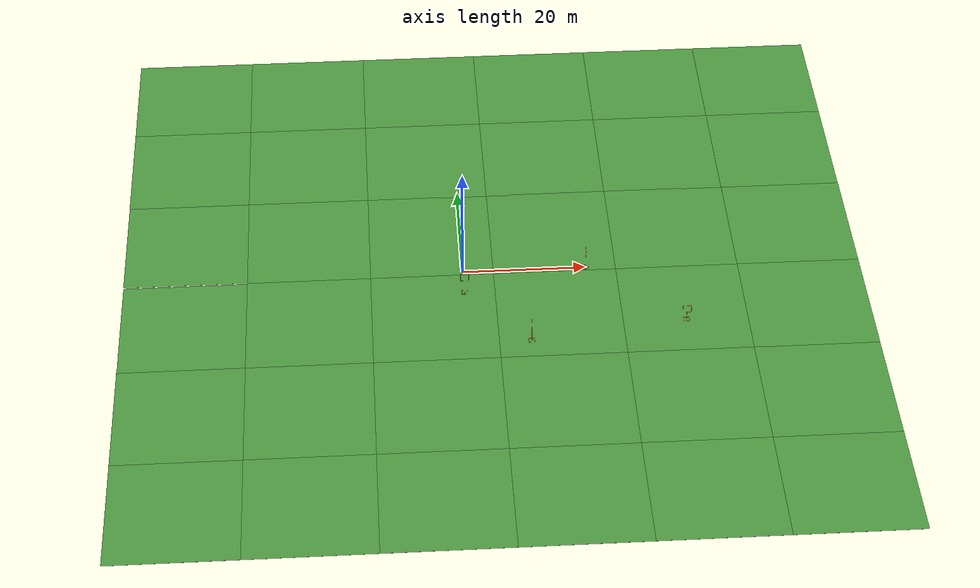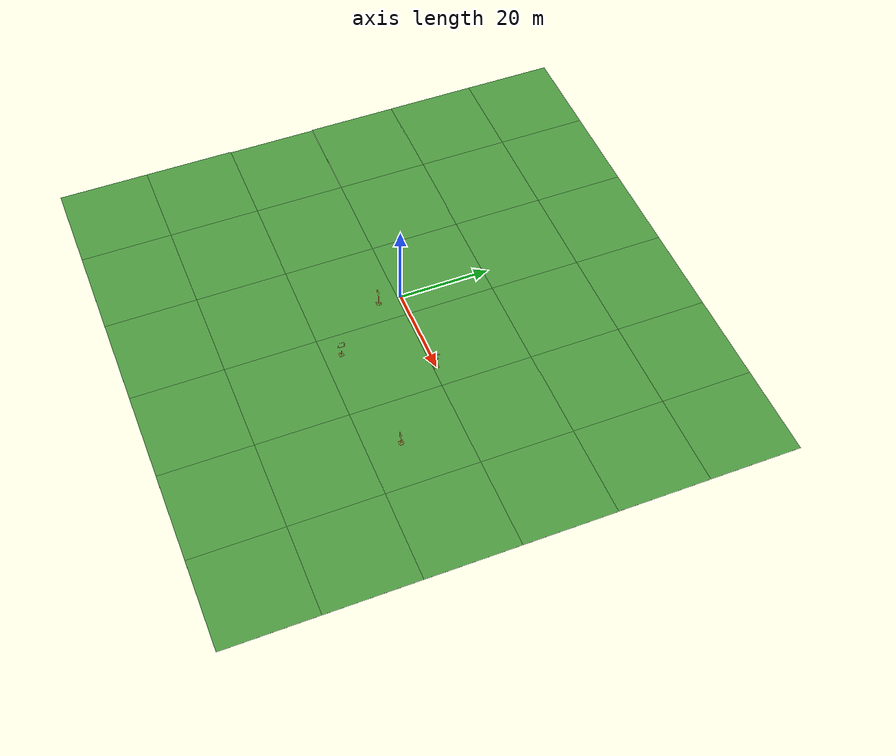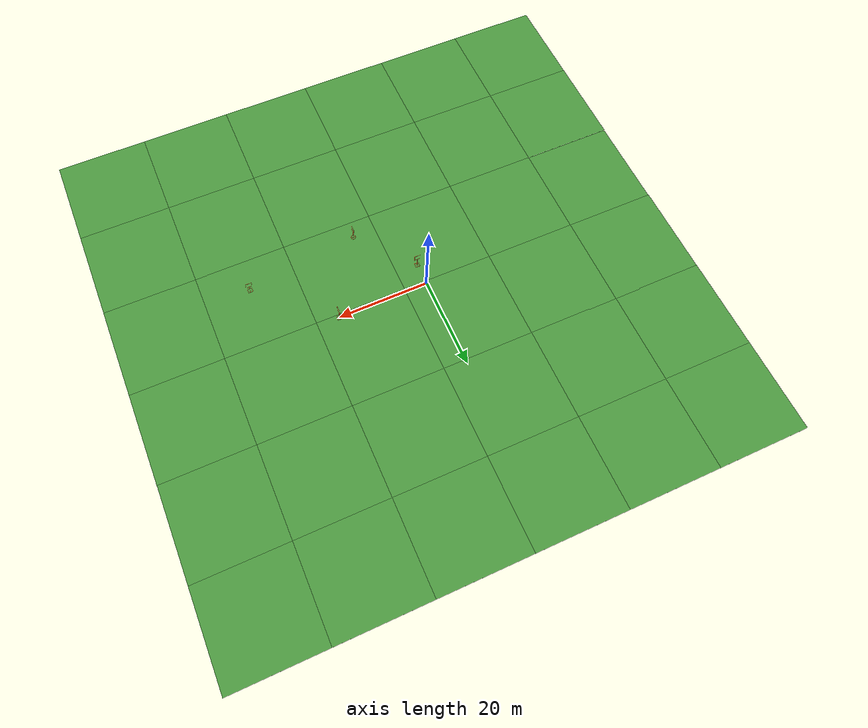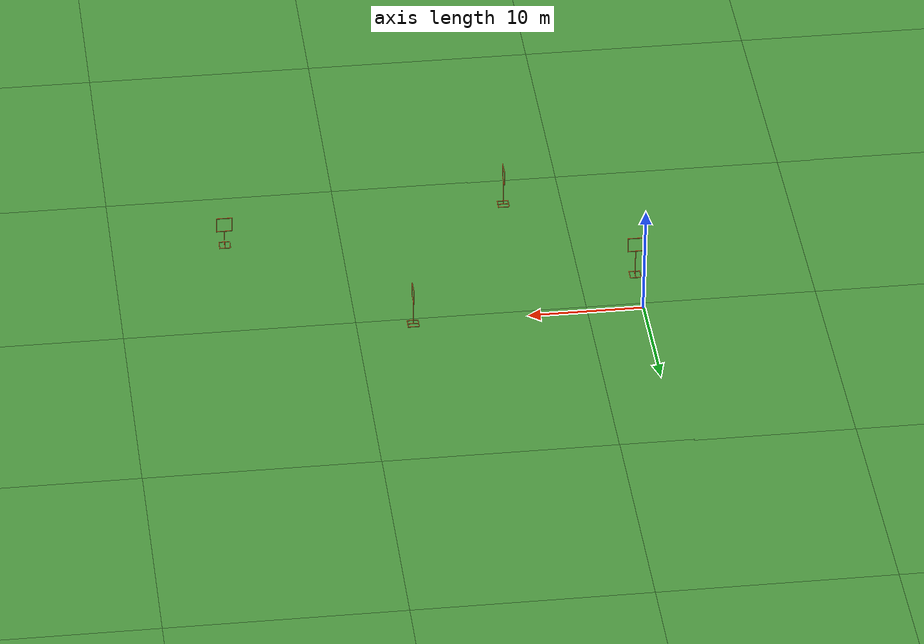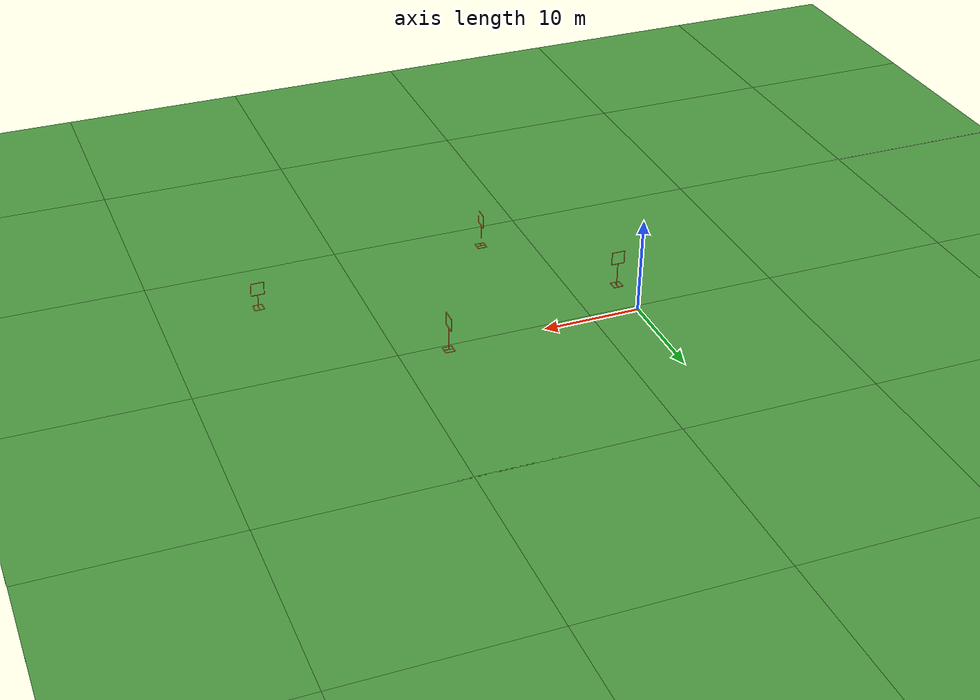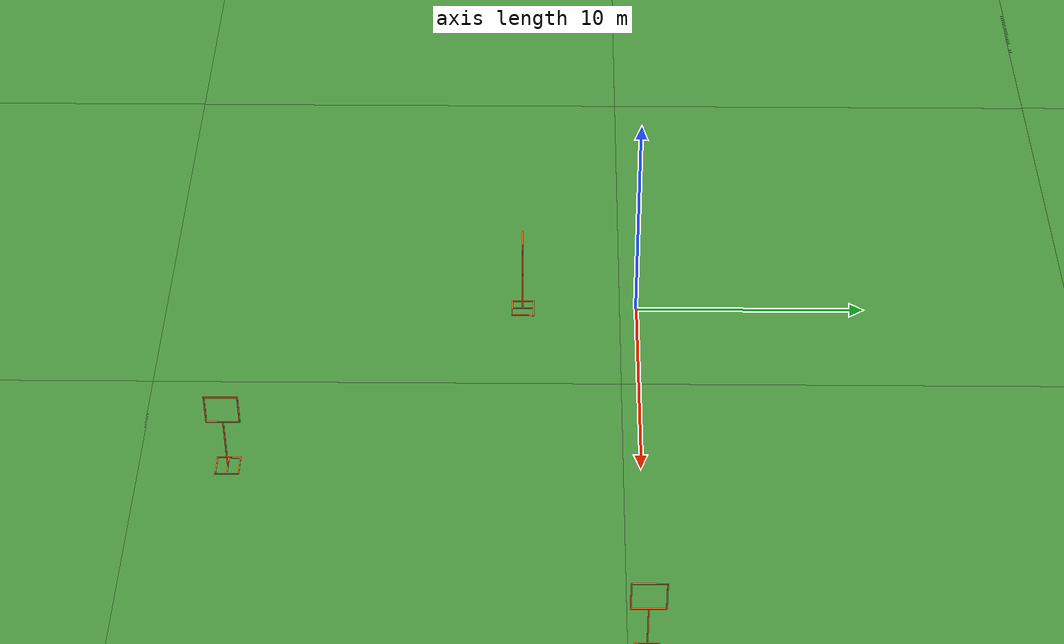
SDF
<sdf version="1.7">
 <world name="default">
  <light name="sun" type="directional">
   <pose>0 0 10 0 -0 0</pose>
   <diffuse>0.8 0.8 0.8 1</diffuse>
   <specular>0.2 0.2 0.2 1</specular>
   <attenuation>
    <range>1000</range>
    <constant>0.9</constant>
    <linear>0.01</linear>
    <quadratic>0.001</quadratic>
   </attenuation>
   <direction>-0.5 0.1 -0.9</direction>
   <spot><inner_angle>0</inner_angle><outer_angle>0</outer_angle><falloff>0</falloff></spot>
  </light>
  <gravity>0 0 -9.8</gravity>
  <magnetic_field>6e-06 2.3e-05 -4.2e-05</magnetic_field>
  <atmosphere type="adiabatic"/>
  <physics type="ode">
   <max_step_size>0.001</max_step_size>
   <real_time_factor>1</real_time_factor>
   <real_time_update_rate>1000</real_time_update_rate>
  </physics>
  <scene><ambient>0.4 0.4 0.4 1</ambient><background>0.7 0.7 0.7 1</background><shadows>1</shadows></scene>
  <spherical_coordinates>
   <surface_model>EARTH_WGS84</surface_model>
   <latitude_deg>0</latitude_deg>
   <longitude_deg>0</longitude_deg>
   <elevation>0</elevation>
   <heading_deg>0</heading_deg>
  </spherical_coordinates>
  <model name="grass_plane">
   <static>1</static>
   <link name="link">
    <collision name="collision">
     <geometry><plane><normal>0 0 1</normal><size>500 500</size></plane></geometry>
     <surface><friction><ode><mu>0.5</mu><mu2>0.5</mu2></ode></friction></surface>
    </collision>
    <visual name="visual_0">
     <pose>-40 -40 0 0 -0 0</pose>
     <cast_shadows>0</cast_shadows>
     <geometry><plane><normal>0 0 1</normal><size>20 20</size></plane></geometry>
     <material>
      <script>
       <uri>model://grass_plane/materials/scripts</uri>
       <uri>model://grass_plane/materials/textures</uri>
       <name>vrc/grass</name>
      </script>
     </material>
    </visual>
    <visual name="visual_1">
     <pose>-20 -40 0 0 -0 0</pose>
     <cast_shadows>0</cast_shadows>
     <geometry><plane><normal>0 0 1</normal><size>20 20</size></plane></geometry>
     <material>
      <script>
       <uri>model://grass_plane/materials/scripts</uri>
       <uri>model://grass_plane/materials/textures</uri>
       <name>vrc/grass</name>
      </script>
     </material>
    </visual>
    <visual name="visual_2">
     <pose>0 -40 0 0 -0 0</pose>
     <cast_shadows>0</cast_shadows>
     <geometry><plane><normal>0 0 1</normal><size>20 20</size></plane></geometry>
     <material>
      <script>
       <uri>model://grass_plane/materials/scripts</uri>
       <uri>model://grass_plane/materials/textures</uri>
       <name>vrc/grass</name>
      </script>
     </material>
    </visual>
    <visual name="visual_3">
     <pose>20 -40 0 0 -0 0</pose>
     <cast_shadows>0</cast_shadows>
     <geometry><plane><normal>0 0 1</normal><size>20 20</size></plane></geometry>
     <material>
      <script>
       <uri>model://grass_plane/materials/scripts</uri>
       <uri>model://grass_plane/materials/textures</uri>
       <name>vrc/grass</name>
      </script>
     </material>
    </visual>
    <visual name="visual_4">
     <pose>40 -40 0 0 -0 0</pose>
     <cast_shadows>0</cast_shadows>
     <geometry><plane><normal>0 0 1</normal><size>20 20</size></plane></geometry>
     <material>
      <script>
       <uri>model://grass_plane/materials/scripts</uri>
       <uri>model://grass_plane/materials/textures</uri>
       <name>vrc/grass</name>
      </script>
     </material>
    </visual>
    <visual name="visual_5">
     <pose>60 -40 0 0 -0 0</pose>
     <cast_shadows>0</cast_shadows>
     <geometry><plane><normal>0 0 1</normal><size>20 20</size></plane></geometry>
     <material>
      <script>
       <uri>model://grass_plane/materials/scripts</uri>
       <uri>model://grass_plane/materials/textures</uri>
       <name>vrc/grass</name>
      </script>
     </material>
    </visual>
    <visual name="visual_6">
     <pose>-40 -20 0 0 -0 0</pose>
     <cast_shadows>0</cast_shadows>
     <geometry><plane><normal>0 0 1</normal><size>20 20</size></plane></geometry>
     <material>
      <script>
       <uri>model://grass_plane/materials/scripts</uri>
       <uri>model://grass_plane/materials/textures</uri>
       <name>vrc/grass</name>
      </script>
     </material>
    </visual>
    <visual name="visual_7">
     <pose>-20 -20 0 0 -0 0</pose>
     <cast_shadows>0</cast_shadows>
     <geometry><plane><normal>0 0 1</normal><size>20 20</size></plane></geometry>
     <material>
      <script>
       <uri>model://grass_plane/materials/scripts</uri>
       <uri>model://grass_plane/materials/textures</uri>
       <name>vrc/grass</name>
      </script>
     </material>
    </visual>
    <visual name="visual_8">
     <pose>0 -20 0 0 -0 0</pose>
     <cast_shadows>0</cast_shadows>
     <geometry><plane><normal>0 0 1</normal><size>20 20</size></plane></geometry>
     <material>
      <script>
       <uri>model://grass_plane/materials/scripts</uri>
       <uri>model://grass_plane/materials/textures</uri>
       <name>vrc/grass</name>
      </script>
     </material>
    </visual>
    <visual name="visual_9">
     <pose>20 -20 0 0 -0 0</pose>
     <cast_shadows>0</cast_shadows>
     <geometry><plane><normal>0 0 1</normal><size>20 20</size></plane></geometry>
     <material>
      <script>
       <uri>model://grass_plane/materials/scripts</uri>
       <uri>model://grass_plane/materials/textures</uri>
       <name>vrc/grass</name>
      </script>
     </material>
    </visual>
    <visual name="visual_10">
     <pose>40 -20 0 0 -0 0</pose>
     <cast_shadows>0</cast_shadows>
     <geometry><plane><normal>0 0 1</normal><size>20 20</size></plane></geometry>
     <material>
      <script>
       <uri>model://grass_plane/materials/scripts</uri>
       <uri>model://grass_plane/materials/textures</uri>
       <name>vrc/grass</name>
      </script>
     </material>
    </visual>
    <visual name="visual_11">
     <pose>60 -20 0 0 -0 0</pose>
     <cast_shadows>0</cast_shadows>
     <geometry><plane><normal>0 0 1</normal><size>20 20</size></plane></geometry>
     <material>
      <script>
       <uri>model://grass_plane/materials/scripts</uri>
       <uri>model://grass_plane/materials/textures</uri>
       <name>vrc/grass</name>
      </script>
     </material>
    </visual>
   </link>
   <pose>-5.11767 29.2655 0 0 -0 0</pose>
  </model>
  <model name="grass_plane_0">
   <static>1</static>
   <link name="link">
    <collision name="collision">
     <geometry><plane><normal>0 0 1</normal><size>500 500</size></plane></geometry>
     <surface><friction><ode><mu>0.5</mu><mu2>0.5</mu2></ode></friction></surface>
    </collision>
    <visual name="visual_0">
     <pose>-40 -40 0 0 -0 0</pose>
     <cast_shadows>0</cast_shadows>
     <geometry><plane><normal>0 0 1</normal><size>20 20</size></plane></geometry>
     <material>
      <script>
       <uri>model://grass_plane/materials/scripts</uri>
       <uri>model://grass_plane/materials/textures</uri>
       <name>vrc/grass</name>
      </script>
     </material>
    </visual>
    <visual name="visual_1">
     <pose>-20 -40 0 0 -0 0</pose>
     <cast_shadows>0</cast_shadows>
     <geometry><plane><normal>0 0 1</normal><size>20 20</size></plane></geometry>
     <material>
      <script>
       <uri>model://grass_plane/materials/scripts</uri>
       <uri>model://grass_plane/materials/textures</uri>
       <name>vrc/grass</name>
      </script>
     </material>
    </visual>
    <visual name="visual_2">
     <pose>0 -40 0 0 -0 0</pose>
     <cast_shadows>0</cast_shadows>
     <geometry><plane><normal>0 0 1</normal><size>20 20</size></plane></geometry>
     <material>
      <script>
       <uri>model://grass_plane/materials/scripts</uri>
       <uri>model://grass_plane/materials/textures</uri>
       <name>vrc/grass</name>
      </script>
     </material>
    </visual>
    <visual name="visual_3">
     <pose>20 -40 0 0 -0 0</pose>
     <cast_shadows>0</cast_shadows>
     <geometry><plane><normal>0 0 1</normal><size>20 20</size></plane></geometry>
     <material>
      <script>
       <uri>model://grass_plane/materials/scripts</uri>
       <uri>model://grass_plane/materials/textures</uri>
       <name>vrc/grass</name>
      </script>
     </material>
    </visual>
    <visual name="visual_4">
     <pose>40 -40 0 0 -0 0</pose>
     <cast_shadows>0</cast_shadows>
     <geometry><plane><normal>0 0 1</normal><size>20 20</size></plane></geometry>
     <material>
      <script>
       <uri>model://grass_plane/materials/scripts</uri>
       <uri>model://grass_plane/materials/textures</uri>
       <name>vrc/grass</name>
      </script>
     </material>
    </visual>
    <visual name="visual_5">
     <pose>60 -40 0 0 -0 0</pose>
     <cast_shadows>0</cast_shadows>
     <geometry><plane><normal>0 0 1</normal><size>20 20</size></plane></geometry>
     <material>
      <script>
       <uri>model://grass_plane/materials/scripts</uri>
       <uri>model://grass_plane/materials/textures</uri>
       <name>vrc/grass</name>
      </script>
     </material>
    </visual>
    <visual name="visual_6">
     <pose>-40 -20 0 0 -0 0</pose>
     <cast_shadows>0</cast_shadows>
     <geometry><plane><normal>0 0 1</normal><size>20 20</size></plane></geometry>
     <material>
      <script>
       <uri>model://grass_plane/materials/scripts</uri>
       <uri>model://grass_plane/materials/textures</uri>
       <name>vrc/grass</name>
      </script>
     </material>
    </visual>
    <visual name="visual_7">
     <pose>-20 -20 0 0 -0 0</pose>
     <cast_shadows>0</cast_shadows>
     <geometry><plane><normal>0 0 1</normal><size>20 20</size></plane></geometry>
     <material>
      <script>
       <uri>model://grass_plane/materials/scripts</uri>
       <uri>model://grass_plane/materials/textures</uri>
       <name>vrc/grass</name>
      </script>
     </material>
    </visual>
    <visual name="visual_8">
     <pose>0 -20 0 0 -0 0</pose>
     <cast_shadows>0</cast_shadows>
     <geometry><plane><normal>0 0 1</normal><size>20 20</size></plane></geometry>
     <material>
      <script>
       <uri>model://grass_plane/materials/scripts</uri>
       <uri>model://grass_plane/materials/textures</uri>
       <name>vrc/grass</name>
      </script>
     </material>
    </visual>
    <visual name="visual_9">
     <pose>20 -20 0 0 -0 0</pose>
     <cast_shadows>0</cast_shadows>
     <geometry><plane><normal>0 0 1</normal><size>20 20</size></plane></geometry>
     <material>
      <script>
       <uri>model://grass_plane/materials/scripts</uri>
       <uri>model://grass_plane/materials/textures</uri>
       <name>vrc/grass</name>
      </script>
     </material>
    </visual>
    <visual name="visual_10">
     <pose>40 -20 0 0 -0 0</pose>
     <cast_shadows>0</cast_shadows>
     <geometry><plane><normal>0 0 1</normal><size>20 20</size></plane></geometry>
     <material>
      <script>
       <uri>model://grass_plane/materials/scripts</uri>
       <uri>model://grass_plane/materials/textures</uri>
       <name>vrc/grass</name>
      </script>
     </material>
    </visual>
    <visual name="visual_11">
     <pose>60 -20 0 0 -0 0</pose>
     <cast_shadows>0</cast_shadows>
     <geometry><plane><normal>0 0 1</normal><size>20 20</size></plane></geometry>
     <material>
      <script>
       <uri>model://grass_plane/materials/scripts</uri>
       <uri>model://grass_plane/materials/textures</uri>
       <name>vrc/grass</name>
      </script>
     </material>
    </visual>
   </link>
   <pose>-5.12978 -10.6715 0 0 -0 0</pose>
  </model>
  <model name="grass_plane_1">
   <static>1</static>
   <link name="link">
    <collision name="collision">
     <geometry><plane><normal>0 0 1</normal><size>500 500</size></plane></geometry>
     <surface><friction><ode><mu>0.5</mu><mu2>0.5</mu2></ode></friction></surface>
    </collision>
    <visual name="visual_0">
     <pose>-40 -40 0 0 -0 0</pose>
     <cast_shadows>0</cast_shadows>
     <geometry><plane><normal>0 0 1</normal><size>20 20</size></plane></geometry>
     <material>
      <script>
       <uri>model://grass_plane/materials/scripts</uri>
       <uri>model://grass_plane/materials/textures</uri>
       <name>vrc/grass</name>
      </script>
     </material>
    </visual>
    <visual name="visual_1">
     <pose>-20 -40 0 0 -0 0</pose>
     <cast_shadows>0</cast_shadows>
     <geometry><plane><normal>0 0 1</normal><size>20 20</size></plane></geometry>
     <material>
      <script>
       <uri>model://grass_plane/materials/scripts</uri>
       <uri>model://grass_plane/materials/textures</uri>
       <name>vrc/grass</name>
      </script>
     </material>
    </visual>
    <visual name="visual_2">
     <pose>0 -40 0 0 -0 0</pose>
     <cast_shadows>0</cast_shadows>
     <geometry><plane><normal>0 0 1</normal><size>20 20</size></plane></geometry>
     <material>
      <script>
       <uri>model://grass_plane/materials/scripts</uri>
       <uri>model://grass_plane/materials/textures</uri>
       <name>vrc/grass</name>
      </script>
     </material>
    </visual>
    <visual name="visual_3">
     <pose>20 -40 0 0 -0 0</pose>
     <cast_shadows>0</cast_shadows>
     <geometry><plane><normal>0 0 1</normal><size>20 20</size></plane></geometry>
     <material>
      <script>
       <uri>model://grass_plane/materials/scripts</uri>
       <uri>model://grass_plane/materials/textures</uri>
       <name>vrc/grass</name>
      </script>
     </material>
    </visual>
    <visual name="visual_4">
     <pose>40 -40 0 0 -0 0</pose>
     <cast_shadows>0</cast_shadows>
     <geometry><plane><normal>0 0 1</normal><size>20 20</size></plane></geometry>
     <material>
      <script>
       <uri>model://grass_plane/materials/scripts</uri>
       <uri>model://grass_plane/materials/textures</uri>
       <name>vrc/grass</name>
      </script>
     </material>
    </visual>
    <visual name="visual_5">
     <pose>60 -40 0 0 -0 0</pose>
     <cast_shadows>0</cast_shadows>
     <geometry><plane><normal>0 0 1</normal><size>20 20</size></plane></geometry>
     <material>
      <script>
       <uri>model://grass_plane/materials/scripts</uri>
       <uri>model://grass_plane/materials/textures</uri>
       <name>vrc/grass</name>
      </script>
     </material>
    </visual>
    <visual name="visual_6">
     <pose>-40 -20 0 0 -0 0</pose>
     <cast_shadows>0</cast_shadows>
     <geometry><plane><normal>0 0 1</normal><size>20 20</size></plane></geometry>
     <material>
      <script>
       <uri>model://grass_plane/materials/scripts</uri>
       <uri>model://grass_plane/materials/textures</uri>
       <name>vrc/grass</name>
      </script>
     </material>
    </visual>
    <visual name="visual_7">
     <pose>-20 -20 0 0 -0 0</pose>
     <cast_shadows>0</cast_shadows>
     <geometry><plane><normal>0 0 1</normal><size>20 20</size></plane></geometry>
     <material>
      <script>
       <uri>model://grass_plane/materials/scripts</uri>
       <uri>model://grass_plane/materials/textures</uri>
       <name>vrc/grass</name>
      </script>
     </material>
    </visual>
    <visual name="visual_8">
     <pose>0 -20 0 0 -0 0</pose>
     <cast_shadows>0</cast_shadows>
     <geometry><plane><normal>0 0 1</normal><size>20 20</size></plane></geometry>
     <material>
      <script>
       <uri>model://grass_plane/materials/scripts</uri>
       <uri>model://grass_plane/materials/textures</uri>
       <name>vrc/grass</name>
      </script>
     </material>
    </visual>
    <visual name="visual_9">
     <pose>20 -20 0 0 -0 0</pose>
     <cast_shadows>0</cast_shadows>
     <geometry><plane><normal>0 0 1</normal><size>20 20</size></plane></geometry>
     <material>
      <script>
       <uri>model://grass_plane/materials/scripts</uri>
       <uri>model://grass_plane/materials/textures</uri>
       <name>vrc/grass</name>
      </script>
     </material>
    </visual>
    <visual name="visual_10">
     <pose>40 -20 0 0 -0 0</pose>
     <cast_shadows>0</cast_shadows>
     <geometry><plane><normal>0 0 1</normal><size>20 20</size></plane></geometry>
     <material>
      <script>
       <uri>model://grass_plane/materials/scripts</uri>
       <uri>model://grass_plane/materials/textures</uri>
       <name>vrc/grass</name>
      </script>
     </material>
    </visual>
    <visual name="visual_11">
     <pose>60 -20 0 0 -0 0</pose>
     <cast_shadows>0</cast_shadows>
     <geometry><plane><normal>0 0 1</normal><size>20 20</size></plane></geometry>
     <material>
      <script>
       <uri>model://grass_plane/materials/scripts</uri>
       <uri>model://grass_plane/materials/textures</uri>
       <name>vrc/grass</name>
      </script>
     </material>
    </visual>
   </link>
   <pose>-5.14384 69.1271 0 0 -0 0</pose>
  </model>
  <model name="adr2017_Large_Gate">
   <link name="link">
    <pose>0 0 1.25 0 -0 0</pose>
    <inertial>
     <mass>1</mass>
     <inertia>
      <ixx>0.166667</ixx>
      <ixy>0</ixy>
      <ixz>0</ixz>
      <iyy>0.166667</iyy>
      <iyz>0</iyz>
      <izz>0.166667</izz>
     </inertia>
    </inertial>
    <visual name="visual">
     <geometry><box><size>0.05 0.05 2.5</size></box></geometry>
     <material>
      <script><name>Gazebo/Grey</name><uri>file://media/materials/scripts/gazebo.material</uri></script>
      <shader type="vertex"><normal_map>__default__</normal_map></shader>
      <ambient>0.976 0.484 0.164 1</ambient>
      <diffuse>0.976 0.484 0.164 1</diffuse>
      <specular>0.01 0.01 0.01 1</specular>
      <emissive>0 0 0 1</emissive>
     </material>
    </visual>
    <collision name="collision">
     <geometry><box><size>0.05 0.05 1.5</size></box></geometry>
     <surface>
      <friction>
       <ode><mu>1</mu><mu2>1</mu2><fdir1>0 0 0</fdir1><slip1>0</slip1><slip2>0</slip2></ode>
       <torsional>
        <coefficient>1</coefficient>
        <patch_radius>0</patch_radius>
        <surface_radius>0</surface_radius>
        <use_patch_radius>1</use_patch_radius>
        <ode><slip>0</slip></ode>
       </torsional>
      </friction>
      <bounce><restitution_coefficient>0</restitution_coefficient><threshold>1e+06</threshold></bounce>
      <contact>
       <collide_without_contact>0</collide_without_contact>
       <collide_without_contact_bitmask>1</collide_without_contact_bitmask>
       <collide_bitmask>1</collide_bitmask>
       <ode>
        <soft_cfm>0</soft_cfm>
        <soft_erp>0.2</soft_erp>
        <kp>1e+13</kp>
        <kd>1</kd>
        <max_vel>0.01</max_vel>
        <min_depth>0</min_depth>
       </ode>
       <bullet>
        <split_impulse>1</split_impulse>
        <split_impulse_penetration_threshold>-0.01</split_impulse_penetration_threshold>
        <soft_cfm>0</soft_cfm>
        <soft_erp>0.2</soft_erp>
        <kp>1e+13</kp>
        <kd>1</kd>
       </bullet>
      </contact>
     </surface>
    </collision>
   </link>
   <link name="link_2">
    <pose>0 0 0.025 0 -0 0</pose>
    <inertial>
     <mass>1</mass>
     <inertia>
      <ixx>0.166667</ixx>
      <ixy>0</ixy>
      <ixz>0</ixz>
      <iyy>0.166667</iyy>
      <iyz>0</iyz>
      <izz>0.166667</izz>
     </inertia>
    </inertial>
    <visual name="visual">
     <geometry><box><size>0.05 1 0.05</size></box></geometry>
     <material>
      <script><name>Gazebo/Grey</name><uri>file://media/materials/scripts/gazebo.material</uri></script>
      <shader type="vertex"><normal_map>__default__</normal_map></shader>
      <ambient>0.976 0.484 0.164 1</ambient>
      <diffuse>0.976 0.484 0.164 1</diffuse>
      <specular>0.01 0.01 0.01 1</specular>
      <emissive>0 0 0 1</emissive>
     </material>
    </visual>
    <collision name="collision">
     <geometry><box><size>0.05 1 0.05</size></box></geometry>
     <surface>
      <friction>
       <ode><mu>1</mu><mu2>1</mu2><fdir1>0 0 0</fdir1><slip1>0</slip1><slip2>0</slip2></ode>
       <torsional>
        <coefficient>1</coefficient>
        <patch_radius>0</patch_radius>
        <surface_radius>0</surface_radius>
        <use_patch_radius>1</use_patch_radius>
        <ode><slip>0</slip></ode>
       </torsional>
      </friction>
      <bounce><restitution_coefficient>0</restitution_coefficient><threshold>1e+06</threshold></bounce>
      <contact>
       <collide_without_contact>0</collide_without_contact>
       <collide_without_contact_bitmask>1</collide_without_contact_bitmask>
       <collide_bitmask>1</collide_bitmask>
       <ode>
        <soft_cfm>0</soft_cfm>
        <soft_erp>0.2</soft_erp>
        <kp>1e+13</kp>
        <kd>1</kd>
        <max_vel>0.01</max_vel>
        <min_depth>0</min_depth>
       </ode>
       <bullet>
        <split_impulse>1</split_impulse>
        <split_impulse_penetration_threshold>-0.01</split_impulse_penetration_threshold>
        <soft_cfm>0</soft_cfm>
        <soft_erp>0.2</soft_erp>
        <kp>1e+13</kp>
        <kd>1</kd>
       </bullet>
      </contact>
     </surface>
    </collision>
   </link>
   <link name="link_3">
    <pose>0.475 0 0.024 0 -0 0</pose>
    <inertial>
     <mass>1</mass>
     <inertia>
      <ixx>0.166667</ixx>
      <ixy>0</ixy>
      <ixz>0</ixz>
      <iyy>0.166667</iyy>
      <iyz>0</iyz>
      <izz>0.166667</izz>
     </inertia>
    </inertial>
    <visual name="visual">
     <geometry><box><size>0.05 1 0.05</size></box></geometry>
     <material>
      <script><name>Gazebo/Grey</name><uri>file://media/materials/scripts/gazebo.material</uri></script>
      <shader type="vertex"><normal_map>__default__</normal_map></shader>
      <ambient>0.976 0.484 0.164 1</ambient>
      <diffuse>0.976 0.484 0.164 1</diffuse>
      <specular>0.01 0.01 0.01 1</specular>
      <emissive>0 0 0 1</emissive>
     </material>
    </visual>
    <collision name="collision">
     <geometry><box><size>0.05 1 0.05</size></box></geometry>
     <surface>
      <friction>
       <ode><mu>1</mu><mu2>1</mu2><fdir1>0 0 0</fdir1><slip1>0</slip1><slip2>0</slip2></ode>
       <torsional>
        <coefficient>1</coefficient>
        <patch_radius>0</patch_radius>
        <surface_radius>0</surface_radius>
        <use_patch_radius>1</use_patch_radius>
        <ode><slip>0</slip></ode>
       </torsional>
      </friction>
      <bounce><restitution_coefficient>0</restitution_coefficient><threshold>1e+06</threshold></bounce>
      <contact>
       <collide_without_contact>0</collide_without_contact>
       <collide_without_contact_bitmask>1</collide_without_contact_bitmask>
       <collide_bitmask>1</collide_bitmask>
       <ode>
        <soft_cfm>0</soft_cfm>
        <soft_erp>0.2</soft_erp>
        <kp>1e+13</kp>
        <kd>1</kd>
        <max_vel>0.01</max_vel>
        <min_depth>0</min_depth>
       </ode>
       <bullet>
        <split_impulse>1</split_impulse>
        <split_impulse_penetration_threshold>-0.01</split_impulse_penetration_threshold>
        <soft_cfm>0</soft_cfm>
        <soft_erp>0.2</soft_erp>
        <kp>1e+13</kp>
        <kd>1</kd>
       </bullet>
      </contact>
     </surface>
    </collision>
   </link>
   <link name="link_4">
    <pose>-0.475 0 0.024 0 -0 0</pose>
    <inertial>
     <mass>1</mass>
     <inertia>
      <ixx>0.166667</ixx>
      <ixy>0</ixy>
      <ixz>0</ixz>
      <iyy>0.166667</iyy>
      <iyz>0</iyz>
      <izz>0.166667</izz>
     </inertia>
    </inertial>
    <visual name="visual">
     <geometry><box><size>0.05 1 0.05</size></box></geometry>
     <material>
      <script><name>Gazebo/Grey</name><uri>file://media/materials/scripts/gazebo.material</uri></script>
      <shader type="vertex"><normal_map>__default__</normal_map></shader>
      <ambient>0.976 0.484 0.164 1</ambient>
      <diffuse>0.976 0.484 0.164 1</diffuse>
      <specular>0.01 0.01 0.01 1</specular>
      <emissive>0 0 0 1</emissive>
     </material>
    </visual>
    <collision name="collision">
     <geometry><box><size>0.05 1 0.05</size></box></geometry>
     <surface>
      <friction>
       <ode><mu>1</mu><mu2>1</mu2><fdir1>0 0 0</fdir1><slip1>0</slip1><slip2>0</slip2></ode>
       <torsional>
        <coefficient>1</coefficient>
        <patch_radius>0</patch_radius>
        <surface_radius>0</surface_radius>
        <use_patch_radius>1</use_patch_radius>
        <ode><slip>0</slip></ode>
       </torsional>
      </friction>
      <bounce><restitution_coefficient>0</restitution_coefficient><threshold>1e+06</threshold></bounce>
      <contact>
       <collide_without_contact>0</collide_without_contact>
       <collide_without_contact_bitmask>1</collide_without_contact_bitmask>
       <collide_bitmask>1</collide_bitmask>
       <ode>
        <soft_cfm>0</soft_cfm>
        <soft_erp>0.2</soft_erp>
        <kp>1e+13</kp>
        <kd>1</kd>
        <max_vel>0.01</max_vel>
        <min_depth>0</min_depth>
       </ode>
       <bullet>
        <split_impulse>1</split_impulse>
        <split_impulse_penetration_threshold>-0.01</split_impulse_penetration_threshold>
        <soft_cfm>0</soft_cfm>
        <soft_erp>0.2</soft_erp>
        <kp>1e+13</kp>
        <kd>1</kd>
       </bullet>
      </contact>
     </surface>
    </collision>
   </link>
   <link name="link_5">
    <pose>0 0.475 0.025 0 -0 0</pose>
    <inertial>
     <mass>1</mass>
     <inertia>
      <ixx>0.166667</ixx>
      <ixy>0</ixy>
      <ixz>0</ixz>
      <iyy>0.166667</iyy>
      <iyz>0</iyz>
      <izz>0.166667</izz>
     </inertia>
    </inertial>
    <visual name="visual">
     <geometry><box><size>1 0.05 0.05</size></box></geometry>
     <material>
      <script><name>Gazebo/Grey</name><uri>file://media/materials/scripts/gazebo.material</uri></script>
      <shader type="vertex"><normal_map>__default__</normal_map></shader>
      <ambient>0.976 0.484 0.164 1</ambient>
      <diffuse>0.976 0.484 0.164 1</diffuse>
      <specular>0.01 0.01 0.01 1</specular>
      <emissive>0 0 0 1</emissive>
     </material>
    </visual>
    <collision name="collision">
     <geometry><box><size>1 0.05 0.05</size></box></geometry>
     <surface>
      <friction>
       <ode><mu>1</mu><mu2>1</mu2><fdir1>0 0 0</fdir1><slip1>0</slip1><slip2>0</slip2></ode>
       <torsional>
        <coefficient>1</coefficient>
        <patch_radius>0</patch_radius>
        <surface_radius>0</surface_radius>
        <use_patch_radius>1</use_patch_radius>
        <ode><slip>0</slip></ode>
       </torsional>
      </friction>
      <bounce><restitution_coefficient>0</restitution_coefficient><threshold>1e+06</threshold></bounce>
      <contact>
       <collide_without_contact>0</collide_without_contact>
       <collide_without_contact_bitmask>1</collide_without_contact_bitmask>
       <collide_bitmask>1</collide_bitmask>
       <ode>
        <soft_cfm>0</soft_cfm>
        <soft_erp>0.2</soft_erp>
        <kp>1e+13</kp>
        <kd>1</kd>
        <max_vel>0.01</max_vel>
        <min_depth>0</min_depth>
       </ode>
       <bullet>
        <split_impulse>1</split_impulse>
        <split_impulse_penetration_threshold>-0.01</split_impulse_penetration_threshold>
        <soft_cfm>0</soft_cfm>
        <soft_erp>0.2</soft_erp>
        <kp>1e+13</kp>
        <kd>1</kd>
       </bullet>
      </contact>
     </surface>
    </collision>
   </link>
   <link name="link_6">
    <pose>0 -0.475 0.025 0 -0 0</pose>
    <inertial>
     <mass>1</mass>
     <inertia>
      <ixx>0.166667</ixx>
      <ixy>0</ixy>
      <ixz>0</ixz>
      <iyy>0.166667</iyy>
      <iyz>0</iyz>
      <izz>0.166667</izz>
     </inertia>
    </inertial>
    <visual name="visual">
     <geometry><box><size>1 0.05 0.05</size></box></geometry>
     <material>
      <script><name>Gazebo/Grey</name><uri>file://media/materials/scripts/gazebo.material</uri></script>
      <shader type="vertex"><normal_map>__default__</normal_map></shader>
      <ambient>0.976 0.484 0.164 1</ambient>
      <diffuse>0.976 0.484 0.164 1</diffuse>
      <specular>0.01 0.01 0.01 1</specular>
      <emissive>0 0 0 1</emissive>
     </material>
    </visual>
    <collision name="collision">
     <geometry><box><size>1 0.05 0.05</size></box></geometry>
     <surface>
      <friction>
       <ode><mu>1</mu><mu2>1</mu2><fdir1>0 0 0</fdir1><slip1>0</slip1><slip2>0</slip2></ode>
       <torsional>
        <coefficient>1</coefficient>
        <patch_radius>0</patch_radius>
        <surface_radius>0</surface_radius>
        <use_patch_radius>1</use_patch_radius>
        <ode><slip>0</slip></ode>
       </torsional>
      </friction>
      <bounce><restitution_coefficient>0</restitution_coefficient><threshold>1e+06</threshold></bounce>
      <contact>
       <collide_without_contact>0</collide_without_contact>
       <collide_without_contact_bitmask>1</collide_without_contact_bitmask>
       <collide_bitmask>1</collide_bitmask>
       <ode>
        <soft_cfm>0</soft_cfm>
        <soft_erp>0.2</soft_erp>
        <kp>1e+13</kp>
        <kd>1</kd>
        <max_vel>0.01</max_vel>
        <min_depth>0</min_depth>
       </ode>
       <bullet>
        <split_impulse>1</split_impulse>
        <split_impulse_penetration_threshold>-0.01</split_impulse_penetration_threshold>
        <soft_cfm>0</soft_cfm>
        <soft_erp>0.2</soft_erp>
        <kp>1e+13</kp>
        <kd>1</kd>
       </bullet>
      </contact>
     </surface>
    </collision>
   </link>
   <link name="link_7">
    <pose>0 0 3.85 0 -0 0</pose>
    <inertial>
     <mass>1</mass>
     <inertia>
      <ixx>0.166667</ixx>
      <ixy>0</ixy>
      <ixz>0</ixz>
      <iyy>0.166667</iyy>
      <iyz>0</iyz>
      <izz>0.166667</izz>
     </inertia>
    </inertial>
    <visual name="visual">
     <geometry><box><size>1.4 0.05 0.05</size></box></geometry>
     <material>
      <script><name>Gazebo/Grey</name><uri>file://media/materials/scripts/gazebo.material</uri></script>
      <shader type="vertex"><normal_map>__default__</normal_map></shader>
      <ambient>0.976 0.484 0.164 1</ambient>
      <diffuse>0.976 0.484 0.164 1</diffuse>
      <specular>0.01 0.01 0.01 1</specular>
      <emissive>0 0 0 1</emissive>
     </material>
    </visual>
    <collision name="collision">
     <geometry><box><size>1.4 0.05 0.05</size></box></geometry>
     <surface>
      <friction>
       <ode><mu>1</mu><mu2>1</mu2><fdir1>0 0 0</fdir1><slip1>0</slip1><slip2>0</slip2></ode>
       <torsional>
        <coefficient>1</coefficient>
        <patch_radius>0</patch_radius>
        <surface_radius>0</surface_radius>
        <use_patch_radius>1</use_patch_radius>
        <ode><slip>0</slip></ode>
       </torsional>
      </friction>
      <bounce><restitution_coefficient>0</restitution_coefficient><threshold>1e+06</threshold></bounce>
      <contact>
       <collide_without_contact>0</collide_without_contact>
       <collide_without_contact_bitmask>1</collide_without_contact_bitmask>
       <collide_bitmask>1</collide_bitmask>
       <ode>
        <soft_cfm>0</soft_cfm>
        <soft_erp>0.2</soft_erp>
        <kp>1e+13</kp>
        <kd>1</kd>
        <max_vel>0.01</max_vel>
        <min_depth>0</min_depth>
       </ode>
       <bullet>
        <split_impulse>1</split_impulse>
        <split_impulse_penetration_threshold>-0.01</split_impulse_penetration_threshold>
        <soft_cfm>0</soft_cfm>
        <soft_erp>0.2</soft_erp>
        <kp>1e+13</kp>
        <kd>1</kd>
       </bullet>
      </contact>
     </surface>
    </collision>
   </link>
   <link name="link_8">
    <pose>0 0 2.5 0 -0 0</pose>
    <inertial>
     <mass>1</mass>
     <inertia>
      <ixx>0.166667</ixx>
      <ixy>0</ixy>
      <ixz>0</ixz>
      <iyy>0.166667</iyy>
      <iyz>0</iyz>
      <izz>0.166667</izz>
     </inertia>
    </inertial>
    <visual name="visual">
     <geometry><box><size>1.4 0.05 0.05</size></box></geometry>
     <material>
      <script><name>Gazebo/Grey</name><uri>file://media/materials/scripts/gazebo.material</uri></script>
      <shader type="vertex"><normal_map>__default__</normal_map></shader>
      <ambient>0.976 0.484 0.164 1</ambient>
      <diffuse>0.976 0.484 0.164 1</diffuse>
      <specular>0.01 0.01 0.01 1</specular>
      <emissive>0 0 0 1</emissive>
     </material>
    </visual>
    <collision name="collision">
     <geometry><box><size>1.4 0.05 0.05</size></box></geometry>
     <surface>
      <friction>
       <ode><mu>1</mu><mu2>1</mu2><fdir1>0 0 0</fdir1><slip1>0</slip1><slip2>0</slip2></ode>
       <torsional>
        <coefficient>1</coefficient>
        <patch_radius>0</patch_radius>
        <surface_radius>0</surface_radius>
        <use_patch_radius>1</use_patch_radius>
        <ode><slip>0</slip></ode>
       </torsional>
      </friction>
      <bounce><restitution_coefficient>0</restitution_coefficient><threshold>1e+06</threshold></bounce>
      <contact>
       <collide_without_contact>0</collide_without_contact>
       <collide_without_contact_bitmask>1</collide_without_contact_bitmask>
       <collide_bitmask>1</collide_bitmask>
       <ode>
        <soft_cfm>0</soft_cfm>
        <soft_erp>0.2</soft_erp>
        <kp>1e+13</kp>
        <kd>1</kd>
        <max_vel>0.01</max_vel>
        <min_depth>0</min_depth>
       </ode>
       <bullet>
        <split_impulse>1</split_impulse>
        <split_impulse_penetration_threshold>-0.01</split_impulse_penetration_threshold>
        <soft_cfm>0</soft_cfm>
        <soft_erp>0.2</soft_erp>
        <kp>1e+13</kp>
        <kd>1</kd>
       </bullet>
      </contact>
     </surface>
    </collision>
   </link>
   <link name="link_9">
    <pose>-0.675 0 2.475 0 -0 0</pose>
    <inertial>
     <mass>1</mass>
     <inertia>
      <ixx>0.166667</ixx>
      <ixy>0</ixy>
      <ixz>0</ixz>
      <iyy>0.166667</iyy>
      <iyz>0</iyz>
      <izz>0.166667</izz>
     </inertia>
    </inertial>
    <visual name="visual">
     <geometry><box><size>0.05 0.05 1.4</size></box></geometry>
     <material>
      <script><name>Gazebo/Grey</name><uri>file://media/materials/scripts/gazebo.material</uri></script>
      <shader type="vertex"><normal_map>__default__</normal_map></shader>
      <ambient>0.976 0.484 0.164 1</ambient>
      <diffuse>0.976 0.484 0.164 1</diffuse>
      <specular>0.01 0.01 0.01 1</specular>
      <emissive>0 0 0 1</emissive>
     </material>
     <pose>0 0 0.7 0 -0 0</pose>
    </visual>
    <collision name="collision">
     <pose>0 0 0.7 0 -0 0</pose>
     <geometry><box><size>0.05 0.05 1.4</size></box></geometry>
     <surface>
      <friction>
       <ode><mu>1</mu><mu2>1</mu2><fdir1>0 0 0</fdir1><slip1>0</slip1><slip2>0</slip2></ode>
       <torsional>
        <coefficient>1</coefficient>
        <patch_radius>0</patch_radius>
        <surface_radius>0</surface_radius>
        <use_patch_radius>1</use_patch_radius>
        <ode><slip>0</slip></ode>
       </torsional>
      </friction>
      <bounce><restitution_coefficient>0</restitution_coefficient><threshold>1e+06</threshold></bounce>
      <contact>
       <collide_without_contact>0</collide_without_contact>
       <collide_without_contact_bitmask>1</collide_without_contact_bitmask>
       <collide_bitmask>1</collide_bitmask>
       <ode>
        <soft_cfm>0</soft_cfm>
        <soft_erp>0.2</soft_erp>
        <kp>1e+13</kp>
        <kd>1</kd>
        <max_vel>0.01</max_vel>
        <min_depth>0</min_depth>
       </ode>
       <bullet>
        <split_impulse>1</split_impulse>
        <split_impulse_penetration_threshold>-0.01</split_impulse_penetration_threshold>
        <soft_cfm>0</soft_cfm>
        <soft_erp>0.2</soft_erp>
        <kp>1e+13</kp>
        <kd>1</kd>
       </bullet>
      </contact>
     </surface>
    </collision>
   </link>
   <link name="link_10">
    <pose>0.675 0 2.475 0 -0 0</pose>
    <inertial>
     <mass>1</mass>
     <inertia>
      <ixx>0.166667</ixx>
      <ixy>0</ixy>
      <ixz>0</ixz>
      <iyy>0.166667</iyy>
      <iyz>0</iyz>
      <izz>0.166667</izz>
     </inertia>
    </inertial>
    <visual name="visual">
     <geometry><box><size>0.05 0.05 1.4</size></box></geometry>
     <material>
      <script><name>Gazebo/Grey</name><uri>file://media/materials/scripts/gazebo.material</uri></script>
      <shader type="vertex"><normal_map>__default__</normal_map></shader>
      <ambient>0.976 0.484 0.164 1</ambient>
      <diffuse>0.976 0.484 0.164 1</diffuse>
      <specular>0.01 0.01 0.01 1</specular>
      <emissive>0 0 0 1</emissive>
     </material>
     <pose>0 0 0.7 0 -0 0</pose>
    </visual>
    <collision name="collision">
     <pose>0 0 0.7 0 -0 0</pose>
     <geometry><box><size>0.05 0.05 1.4</size></box></geometry>
     <surface>
      <friction>
       <ode><mu>1</mu><mu2>1</mu2><fdir1>0 0 0</fdir1><slip1>0</slip1><slip2>0</slip2></ode>
       <torsional>
        <coefficient>1</coefficient>
        <patch_radius>0</patch_radius>
        <surface_radius>0</surface_radius>
        <use_patch_radius>1</use_patch_radius>
        <ode><slip>0</slip></ode>
       </torsional>
      </friction>
      <bounce><restitution_coefficient>0</restitution_coefficient><threshold>1e+06</threshold></bounce>
      <contact>
       <collide_without_contact>0</collide_without_contact>
       <collide_without_contact_bitmask>1</collide_without_contact_bitmask>
       <collide_bitmask>1</collide_bitmask>
       <ode>
        <soft_cfm>0</soft_cfm>
        <soft_erp>0.2</soft_erp>
        <kp>1e+13</kp>
        <kd>1</kd>
        <max_vel>0.01</max_vel>
        <min_depth>0</min_depth>
       </ode>
       <bullet>
        <split_impulse>1</split_impulse>
        <split_impulse_penetration_threshold>-0.01</split_impulse_penetration_threshold>
        <soft_cfm>0</soft_cfm>
        <soft_erp>0.2</soft_erp>
        <kp>1e+13</kp>
        <kd>1</kd>
       </bullet>
      </contact>
     </surface>
    </collision>
   </link>
   <static>1</static>
   <pose>20 0 0 0 -0 1.57</pose>
  </model>
  <model name="adr2017_Small_Gate">
   <link name="link">
    <pose>0 0 0.75 0 -0 0</pose>
    <inertial>
     <mass>1</mass>
     <inertia>
      <ixx>0.166667</ixx>
      <ixy>0</ixy>
      <ixz>0</ixz>
      <iyy>0.166667</iyy>
      <iyz>0</iyz>
      <izz>0.166667</izz>
     </inertia>
    </inertial>
    <visual name="visual">
     <geometry><box><size>0.05 0.05 1.5</size></box></geometry>
     <material>
      <script><name>Gazebo/Grey</name><uri>file://media/materials/scripts/gazebo.material</uri></script>
      <shader type="vertex"><normal_map>__default__</normal_map></shader>
      <ambient>0.976 0.484 0.164 1</ambient>
      <diffuse>0.976 0.484 0.164 1</diffuse>
      <specular>0.01 0.01 0.01 1</specular>
      <emissive>0 0 0 1</emissive>
     </material>
    </visual>
    <collision name="collision">
     <geometry><box><size>0.05 0.05 1.5</size></box></geometry>
     <surface>
      <friction>
       <ode><mu>1</mu><mu2>1</mu2><fdir1>0 0 0</fdir1><slip1>0</slip1><slip2>0</slip2></ode>
       <torsional>
        <coefficient>1</coefficient>
        <patch_radius>0</patch_radius>
        <surface_radius>0</surface_radius>
        <use_patch_radius>1</use_patch_radius>
        <ode><slip>0</slip></ode>
       </torsional>
      </friction>
      <bounce><restitution_coefficient>0</restitution_coefficient><threshold>1e+06</threshold></bounce>
      <contact>
       <collide_without_contact>0</collide_without_contact>
       <collide_without_contact_bitmask>1</collide_without_contact_bitmask>
       <collide_bitmask>1</collide_bitmask>
       <ode>
        <soft_cfm>0</soft_cfm>
        <soft_erp>0.2</soft_erp>
        <kp>1e+13</kp>
        <kd>1</kd>
        <max_vel>0.01</max_vel>
        <min_depth>0</min_depth>
       </ode>
       <bullet>
        <split_impulse>1</split_impulse>
        <split_impulse_penetration_threshold>-0.01</split_impulse_penetration_threshold>
        <soft_cfm>0</soft_cfm>
        <soft_erp>0.2</soft_erp>
        <kp>1e+13</kp>
        <kd>1</kd>
       </bullet>
      </contact>
     </surface>
    </collision>
   </link>
   <link name="link_2">
    <pose>0 0 0.025 0 -0 0</pose>
    <inertial>
     <mass>1</mass>
     <inertia>
      <ixx>0.166667</ixx>
      <ixy>0</ixy>
      <ixz>0</ixz>
      <iyy>0.166667</iyy>
      <iyz>0</iyz>
      <izz>0.166667</izz>
     </inertia>
    </inertial>
    <visual name="visual">
     <geometry><box><size>0.05 1 0.05</size></box></geometry>
     <material>
      <script><name>Gazebo/Grey</name><uri>file://media/materials/scripts/gazebo.material</uri></script>
      <shader type="vertex"><normal_map>__default__</normal_map></shader>
      <ambient>0.976 0.484 0.164 1</ambient>
      <diffuse>0.976 0.484 0.164 1</diffuse>
      <specular>0.01 0.01 0.01 1</specular>
      <emissive>0 0 0 1</emissive>
     </material>
    </visual>
    <collision name="collision">
     <geometry><box><size>0.05 1 0.05</size></box></geometry>
     <surface>
      <friction>
       <ode><mu>1</mu><mu2>1</mu2><fdir1>0 0 0</fdir1><slip1>0</slip1><slip2>0</slip2></ode>
       <torsional>
        <coefficient>1</coefficient>
        <patch_radius>0</patch_radius>
        <surface_radius>0</surface_radius>
        <use_patch_radius>1</use_patch_radius>
        <ode><slip>0</slip></ode>
       </torsional>
      </friction>
      <bounce><restitution_coefficient>0</restitution_coefficient><threshold>1e+06</threshold></bounce>
      <contact>
       <collide_without_contact>0</collide_without_contact>
       <collide_without_contact_bitmask>1</collide_without_contact_bitmask>
       <collide_bitmask>1</collide_bitmask>
       <ode>
        <soft_cfm>0</soft_cfm>
        <soft_erp>0.2</soft_erp>
        <kp>1e+13</kp>
        <kd>1</kd>
        <max_vel>0.01</max_vel>
        <min_depth>0</min_depth>
       </ode>
       <bullet>
        <split_impulse>1</split_impulse>
        <split_impulse_penetration_threshold>-0.01</split_impulse_penetration_threshold>
        <soft_cfm>0</soft_cfm>
        <soft_erp>0.2</soft_erp>
        <kp>1e+13</kp>
        <kd>1</kd>
       </bullet>
      </contact>
     </surface>
    </collision>
   </link>
   <link name="link_3">
    <pose>0.475 0 0.024 0 -0 0</pose>
    <inertial>
     <mass>1</mass>
     <inertia>
      <ixx>0.166667</ixx>
      <ixy>0</ixy>
      <ixz>0</ixz>
      <iyy>0.166667</iyy>
      <iyz>0</iyz>
      <izz>0.166667</izz>
     </inertia>
    </inertial>
    <visual name="visual">
     <geometry><box><size>0.05 1 0.05</size></box></geometry>
     <material>
      <script><name>Gazebo/Grey</name><uri>file://media/materials/scripts/gazebo.material</uri></script>
      <shader type="vertex"><normal_map>__default__</normal_map></shader>
      <ambient>0.976 0.484 0.164 1</ambient>
      <diffuse>0.976 0.484 0.164 1</diffuse>
      <specular>0.01 0.01 0.01 1</specular>
      <emissive>0 0 0 1</emissive>
     </material>
    </visual>
    <collision name="collision">
     <geometry><box><size>0.05 1 0.05</size></box></geometry>
     <surface>
      <friction>
       <ode><mu>1</mu><mu2>1</mu2><fdir1>0 0 0</fdir1><slip1>0</slip1><slip2>0</slip2></ode>
       <torsional>
        <coefficient>1</coefficient>
        <patch_radius>0</patch_radius>
        <surface_radius>0</surface_radius>
        <use_patch_radius>1</use_patch_radius>
        <ode><slip>0</slip></ode>
       </torsional>
      </friction>
      <bounce><restitution_coefficient>0</restitution_coefficient><threshold>1e+06</threshold></bounce>
      <contact>
       <collide_without_contact>0</collide_without_contact>
       <collide_without_contact_bitmask>1</collide_without_contact_bitmask>
       <collide_bitmask>1</collide_bitmask>
       <ode>
        <soft_cfm>0</soft_cfm>
        <soft_erp>0.2</soft_erp>
        <kp>1e+13</kp>
        <kd>1</kd>
        <max_vel>0.01</max_vel>
        <min_depth>0</min_depth>
       </ode>
       <bullet>
        <split_impulse>1</split_impulse>
        <split_impulse_penetration_threshold>-0.01</split_impulse_penetration_threshold>
        <soft_cfm>0</soft_cfm>
        <soft_erp>0.2</soft_erp>
        <kp>1e+13</kp>
        <kd>1</kd>
       </bullet>
      </contact>
     </surface>
    </collision>
   </link>
   <link name="link_4">
    <pose>-0.475 0 0.024 0 -0 0</pose>
    <inertial>
     <mass>1</mass>
     <inertia>
      <ixx>0.166667</ixx>
      <ixy>0</ixy>
      <ixz>0</ixz>
      <iyy>0.166667</iyy>
      <iyz>0</iyz>
      <izz>0.166667</izz>
     </inertia>
    </inertial>
    <visual name="visual">
     <geometry><box><size>0.05 1 0.05</size></box></geometry>
     <material>
      <script><name>Gazebo/Grey</name><uri>file://media/materials/scripts/gazebo.material</uri></script>
      <shader type="vertex"><normal_map>__default__</normal_map></shader>
      <ambient>0.976 0.484 0.164 1</ambient>
      <diffuse>0.976 0.484 0.164 1</diffuse>
      <specular>0.01 0.01 0.01 1</specular>
      <emissive>0 0 0 1</emissive>
     </material>
    </visual>
    <collision name="collision">
     <geometry><box><size>0.05 1 0.05</size></box></geometry>
     <surface>
      <friction>
       <ode><mu>1</mu><mu2>1</mu2><fdir1>0 0 0</fdir1><slip1>0</slip1><slip2>0</slip2></ode>
       <torsional>
        <coefficient>1</coefficient>
        <patch_radius>0</patch_radius>
        <surface_radius>0</surface_radius>
        <use_patch_radius>1</use_patch_radius>
        <ode><slip>0</slip></ode>
       </torsional>
      </friction>
      <bounce><restitution_coefficient>0</restitution_coefficient><threshold>1e+06</threshold></bounce>
      <contact>
       <collide_without_contact>0</collide_without_contact>
       <collide_without_contact_bitmask>1</collide_without_contact_bitmask>
       <collide_bitmask>1</collide_bitmask>
       <ode>
        <soft_cfm>0</soft_cfm>
        <soft_erp>0.2</soft_erp>
        <kp>1e+13</kp>
        <kd>1</kd>
        <max_vel>0.01</max_vel>
        <min_depth>0</min_depth>
       </ode>
       <bullet>
        <split_impulse>1</split_impulse>
        <split_impulse_penetration_threshold>-0.01</split_impulse_penetration_threshold>
        <soft_cfm>0</soft_cfm>
        <soft_erp>0.2</soft_erp>
        <kp>1e+13</kp>
        <kd>1</kd>
       </bullet>
      </contact>
     </surface>
    </collision>
   </link>
   <link name="link_5">
    <pose>0 0.475 0.025 0 -0 0</pose>
    <inertial>
     <mass>1</mass>
     <inertia>
      <ixx>0.166667</ixx>
      <ixy>0</ixy>
      <ixz>0</ixz>
      <iyy>0.166667</iyy>
      <iyz>0</iyz>
      <izz>0.166667</izz>
     </inertia>
    </inertial>
    <visual name="visual">
     <geometry><box><size>1 0.05 0.05</size></box></geometry>
     <material>
      <script><name>Gazebo/Grey</name><uri>file://media/materials/scripts/gazebo.material</uri></script>
      <shader type="vertex"><normal_map>__default__</normal_map></shader>
      <ambient>0.976 0.484 0.164 1</ambient>
      <diffuse>0.976 0.484 0.164 1</diffuse>
      <specular>0.01 0.01 0.01 1</specular>
      <emissive>0 0 0 1</emissive>
     </material>
    </visual>
    <collision name="collision">
     <geometry><box><size>1 0.05 0.05</size></box></geometry>
     <surface>
      <friction>
       <ode><mu>1</mu><mu2>1</mu2><fdir1>0 0 0</fdir1><slip1>0</slip1><slip2>0</slip2></ode>
       <torsional>
        <coefficient>1</coefficient>
        <patch_radius>0</patch_radius>
        <surface_radius>0</surface_radius>
        <use_patch_radius>1</use_patch_radius>
        <ode><slip>0</slip></ode>
       </torsional>
      </friction>
      <bounce><restitution_coefficient>0</restitution_coefficient><threshold>1e+06</threshold></bounce>
      <contact>
       <collide_without_contact>0</collide_without_contact>
       <collide_without_contact_bitmask>1</collide_without_contact_bitmask>
       <collide_bitmask>1</collide_bitmask>
       <ode>
        <soft_cfm>0</soft_cfm>
        <soft_erp>0.2</soft_erp>
        <kp>1e+13</kp>
        <kd>1</kd>
        <max_vel>0.01</max_vel>
        <min_depth>0</min_depth>
       </ode>
       <bullet>
        <split_impulse>1</split_impulse>
        <split_impulse_penetration_threshold>-0.01</split_impulse_penetration_threshold>
        <soft_cfm>0</soft_cfm>
        <soft_erp>0.2</soft_erp>
        <kp>1e+13</kp>
        <kd>1</kd>
       </bullet>
      </contact>
     </surface>
    </collision>
   </link>
   <link name="link_6">
    <pose>0 -0.475 0.025 0 -0 0</pose>
    <inertial>
     <mass>1</mass>
     <inertia>
      <ixx>0.166667</ixx>
      <ixy>0</ixy>
      <ixz>0</ixz>
      <iyy>0.166667</iyy>
      <iyz>0</iyz>
      <izz>0.166667</izz>
     </inertia>
    </inertial>
    <visual name="visual">
     <geometry><box><size>1 0.05 0.05</size></box></geometry>
     <material>
      <script><name>Gazebo/Grey</name><uri>file://media/materials/scripts/gazebo.material</uri></script>
      <shader type="vertex"><normal_map>__default__</normal_map></shader>
      <ambient>0.976 0.484 0.164 1</ambient>
      <diffuse>0.976 0.484 0.164 1</diffuse>
      <specular>0.01 0.01 0.01 1</specular>
      <emissive>0 0 0 1</emissive>
     </material>
    </visual>
    <collision name="collision">
     <geometry><box><size>1 0.05 0.05</size></box></geometry>
     <surface>
      <friction>
       <ode><mu>1</mu><mu2>1</mu2><fdir1>0 0 0</fdir1><slip1>0</slip1><slip2>0</slip2></ode>
       <torsional>
        <coefficient>1</coefficient>
        <patch_radius>0</patch_radius>
        <surface_radius>0</surface_radius>
        <use_patch_radius>1</use_patch_radius>
        <ode><slip>0</slip></ode>
       </torsional>
      </friction>
      <bounce><restitution_coefficient>0</restitution_coefficient><threshold>1e+06</threshold></bounce>
      <contact>
       <collide_without_contact>0</collide_without_contact>
       <collide_without_contact_bitmask>1</collide_without_contact_bitmask>
       <collide_bitmask>1</collide_bitmask>
       <ode>
        <soft_cfm>0</soft_cfm>
        <soft_erp>0.2</soft_erp>
        <kp>1e+13</kp>
        <kd>1</kd>
        <max_vel>0.01</max_vel>
        <min_depth>0</min_depth>
       </ode>
       <bullet>
        <split_impulse>1</split_impulse>
        <split_impulse_penetration_threshold>-0.01</split_impulse_penetration_threshold>
        <soft_cfm>0</soft_cfm>
        <soft_erp>0.2</soft_erp>
        <kp>1e+13</kp>
        <kd>1</kd>
       </bullet>
      </contact>
     </surface>
    </collision>
   </link>
   <link name="link_7">
    <pose>0 0 2.85 0 -0 0</pose>
    <inertial>
     <mass>1</mass>
     <inertia>
      <ixx>0.166667</ixx>
      <ixy>0</ixy>
      <ixz>0</ixz>
      <iyy>0.166667</iyy>
      <iyz>0</iyz>
      <izz>0.166667</izz>
     </inertia>
    </inertial>
    <visual name="visual">
     <geometry><box><size>1.4 0.05 0.05</size></box></geometry>
     <material>
      <script><name>Gazebo/Grey</name><uri>file://media/materials/scripts/gazebo.material</uri></script>
      <shader type="vertex"><normal_map>__default__</normal_map></shader>
      <ambient>0.976 0.484 0.164 1</ambient>
      <diffuse>0.976 0.484 0.164 1</diffuse>
      <specular>0.01 0.01 0.01 1</specular>
      <emissive>0 0 0 1</emissive>
     </material>
    </visual>
    <collision name="collision">
     <geometry><box><size>1.4 0.05 0.05</size></box></geometry>
     <surface>
      <friction>
       <ode><mu>1</mu><mu2>1</mu2><fdir1>0 0 0</fdir1><slip1>0</slip1><slip2>0</slip2></ode>
       <torsional>
        <coefficient>1</coefficient>
        <patch_radius>0</patch_radius>
        <surface_radius>0</surface_radius>
        <use_patch_radius>1</use_patch_radius>
        <ode><slip>0</slip></ode>
       </torsional>
      </friction>
      <bounce><restitution_coefficient>0</restitution_coefficient><threshold>1e+06</threshold></bounce>
      <contact>
       <collide_without_contact>0</collide_without_contact>
       <collide_without_contact_bitmask>1</collide_without_contact_bitmask>
       <collide_bitmask>1</collide_bitmask>
       <ode>
        <soft_cfm>0</soft_cfm>
        <soft_erp>0.2</soft_erp>
        <kp>1e+13</kp>
        <kd>1</kd>
        <max_vel>0.01</max_vel>
        <min_depth>0</min_depth>
       </ode>
       <bullet>
        <split_impulse>1</split_impulse>
        <split_impulse_penetration_threshold>-0.01</split_impulse_penetration_threshold>
        <soft_cfm>0</soft_cfm>
        <soft_erp>0.2</soft_erp>
        <kp>1e+13</kp>
        <kd>1</kd>
       </bullet>
      </contact>
     </surface>
    </collision>
   </link>
   <link name="link_8">
    <pose>0 0 1.5 0 -0 0</pose>
    <inertial>
     <mass>1</mass>
     <inertia>
      <ixx>0.166667</ixx>
      <ixy>0</ixy>
      <ixz>0</ixz>
      <iyy>0.166667</iyy>
      <iyz>0</iyz>
      <izz>0.166667</izz>
     </inertia>
    </inertial>
    <visual name="visual">
     <geometry><box><size>1.4 0.05 0.05</size></box></geometry>
     <material>
      <script><name>Gazebo/Grey</name><uri>file://media/materials/scripts/gazebo.material</uri></script>
      <shader type="vertex"><normal_map>__default__</normal_map></shader>
      <ambient>0.976 0.484 0.164 1</ambient>
      <diffuse>0.976 0.484 0.164 1</diffuse>
      <specular>0.01 0.01 0.01 1</specular>
      <emissive>0 0 0 1</emissive>
     </material>
    </visual>
    <collision name="collision">
     <geometry><box><size>1.4 0.05 0.05</size></box></geometry>
     <surface>
      <friction>
       <ode><mu>1</mu><mu2>1</mu2><fdir1>0 0 0</fdir1><slip1>0</slip1><slip2>0</slip2></ode>
       <torsional>
        <coefficient>1</coefficient>
        <patch_radius>0</patch_radius>
        <surface_radius>0</surface_radius>
        <use_patch_radius>1</use_patch_radius>
        <ode><slip>0</slip></ode>
       </torsional>
      </friction>
      <bounce><restitution_coefficient>0</restitution_coefficient><threshold>1e+06</threshold></bounce>
      <contact>
       <collide_without_contact>0</collide_without_contact>
       <collide_without_contact_bitmask>1</collide_without_contact_bitmask>
       <collide_bitmask>1</collide_bitmask>
       <ode>
        <soft_cfm>0</soft_cfm>
        <soft_erp>0.2</soft_erp>
        <kp>1e+13</kp>
        <kd>1</kd>
        <max_vel>0.01</max_vel>
        <min_depth>0</min_depth>
       </ode>
       <bullet>
        <split_impulse>1</split_impulse>
        <split_impulse_penetration_threshold>-0.01</split_impulse_penetration_threshold>
        <soft_cfm>0</soft_cfm>
        <soft_erp>0.2</soft_erp>
        <kp>1e+13</kp>
        <kd>1</kd>
       </bullet>
      </contact>
     </surface>
    </collision>
   </link>
   <link name="link_9">
    <pose>-0.675 0 1.475 0 -0 0</pose>
    <inertial>
     <mass>1</mass>
     <inertia>
      <ixx>0.166667</ixx>
      <ixy>0</ixy>
      <ixz>0</ixz>
      <iyy>0.166667</iyy>
      <iyz>0</iyz>
      <izz>0.166667</izz>
     </inertia>
    </inertial>
    <visual name="visual">
     <geometry><box><size>0.05 0.05 1.4</size></box></geometry>
     <material>
      <script><name>Gazebo/Grey</name><uri>file://media/materials/scripts/gazebo.material</uri></script>
      <shader type="vertex"><normal_map>__default__</normal_map></shader>
      <ambient>0.976 0.484 0.164 1</ambient>
      <diffuse>0.976 0.484 0.164 1</diffuse>
      <specular>0.01 0.01 0.01 1</specular>
      <emissive>0 0 0 1</emissive>
     </material>
     <pose>0 0 0.7 0 -0 0</pose>
    </visual>
    <collision name="collision">
     <pose>0 0 0.7 0 -0 0</pose>
     <geometry><box><size>0.05 0.05 1.4</size></box></geometry>
     <surface>
      <friction>
       <ode><mu>1</mu><mu2>1</mu2><fdir1>0 0 0</fdir1><slip1>0</slip1><slip2>0</slip2></ode>
       <torsional>
        <coefficient>1</coefficient>
        <patch_radius>0</patch_radius>
        <surface_radius>0</surface_radius>
        <use_patch_radius>1</use_patch_radius>
        <ode><slip>0</slip></ode>
       </torsional>
      </friction>
      <bounce><restitution_coefficient>0</restitution_coefficient><threshold>1e+06</threshold></bounce>
      <contact>
       <collide_without_contact>0</collide_without_contact>
       <collide_without_contact_bitmask>1</collide_without_contact_bitmask>
       <collide_bitmask>1</collide_bitmask>
       <ode>
        <soft_cfm>0</soft_cfm>
        <soft_erp>0.2</soft_erp>
        <kp>1e+13</kp>
        <kd>1</kd>
        <max_vel>0.01</max_vel>
        <min_depth>0</min_depth>
       </ode>
       <bullet>
        <split_impulse>1</split_impulse>
        <split_impulse_penetration_threshold>-0.01</split_impulse_penetration_threshold>
        <soft_cfm>0</soft_cfm>
        <soft_erp>0.2</soft_erp>
        <kp>1e+13</kp>
        <kd>1</kd>
       </bullet>
      </contact>
     </surface>
    </collision>
   </link>
   <link name="link_10">
    <pose>0.675 0 1.475 0 -0 0</pose>
    <inertial>
     <mass>1</mass>
     <inertia>
      <ixx>0.166667</ixx>
      <ixy>0</ixy>
      <ixz>0</ixz>
      <iyy>0.166667</iyy>
      <iyz>0</iyz>
      <izz>0.166667</izz>
     </inertia>
    </inertial>
    <visual name="visual">
     <geometry><box><size>0.05 0.05 1.4</size></box></geometry>
     <material>
      <script><name>Gazebo/Grey</name><uri>file://media/materials/scripts/gazebo.material</uri></script>
      <shader type="vertex"><normal_map>__default__</normal_map></shader>
      <ambient>0.976 0.484 0.164 1</ambient>
      <diffuse>0.976 0.484 0.164 1</diffuse>
      <specular>0.01 0.01 0.01 1</specular>
      <emissive>0 0 0 1</emissive>
     </material>
     <pose>0 0 0.7 0 -0 0</pose>
    </visual>
    <collision name="collision">
     <pose>0 0 0.7 0 -0 0</pose>
     <geometry><box><size>0.05 0.05 1.4</size></box></geometry>
     <surface>
      <friction>
       <ode><mu>1</mu><mu2>1</mu2><fdir1>0 0 0</fdir1><slip1>0</slip1><slip2>0</slip2></ode>
       <torsional>
        <coefficient>1</coefficient>
        <patch_radius>0</patch_radius>
        <surface_radius>0</surface_radius>
        <use_patch_radius>1</use_patch_radius>
        <ode><slip>0</slip></ode>
       </torsional>
      </friction>
      <bounce><restitution_coefficient>0</restitution_coefficient><threshold>1e+06</threshold></bounce>
      <contact>
       <collide_without_contact>0</collide_without_contact>
       <collide_without_contact_bitmask>1</collide_without_contact_bitmask>
       <collide_bitmask>1</collide_bitmask>
       <ode>
        <soft_cfm>0</soft_cfm>
        <soft_erp>0.2</soft_erp>
        <kp>1e+13</kp>
        <kd>1</kd>
        <max_vel>0.01</max_vel>
        <min_depth>0</min_depth>
       </ode>
       <bullet>
        <split_impulse>1</split_impulse>
        <split_impulse_penetration_threshold>-0.01</split_impulse_penetration_threshold>
        <soft_cfm>0</soft_cfm>
        <soft_erp>0.2</soft_erp>
        <kp>1e+13</kp>
        <kd>1</kd>
       </bullet>
      </contact>
     </surface>
    </collision>
   </link>
   <static>1</static>
   <pose>35 -13.5694 0 0 -0 0</pose>
  </model>
  <model name="adr2017_Large_Gate_0">
   <link name="link">
    <pose>0 0 1.25 0 -0 0</pose>
    <inertial>
     <mass>1</mass>
     <inertia>
      <ixx>0.166667</ixx>
      <ixy>0</ixy>
      <ixz>0</ixz>
      <iyy>0.166667</iyy>
      <iyz>0</iyz>
      <izz>0.166667</izz>
     </inertia>
    </inertial>
    <visual name="visual">
     <geometry><box><size>0.05 0.05 2.5</size></box></geometry>
     <material>
      <script><name>Gazebo/Grey</name><uri>file://media/materials/scripts/gazebo.material</uri></script>
      <shader type="vertex"><normal_map>__default__</normal_map></shader>
      <ambient>0.976 0.484 0.164 1</ambient>
      <diffuse>0.976 0.484 0.164 1</diffuse>
      <specular>0.01 0.01 0.01 1</specular>
      <emissive>0 0 0 1</emissive>
     </material>
    </visual>
    <collision name="collision">
     <geometry><box><size>0.05 0.05 1.5</size></box></geometry>
     <surface>
      <friction>
       <ode><mu>1</mu><mu2>1</mu2><fdir1>0 0 0</fdir1><slip1>0</slip1><slip2>0</slip2></ode>
       <torsional>
        <coefficient>1</coefficient>
        <patch_radius>0</patch_radius>
        <surface_radius>0</surface_radius>
        <use_patch_radius>1</use_patch_radius>
        <ode><slip>0</slip></ode>
       </torsional>
      </friction>
      <bounce><restitution_coefficient>0</restitution_coefficient><threshold>1e+06</threshold></bounce>
      <contact>
       <collide_without_contact>0</collide_without_contact>
       <collide_without_contact_bitmask>1</collide_without_contact_bitmask>
       <collide_bitmask>1</collide_bitmask>
       <ode>
        <soft_cfm>0</soft_cfm>
        <soft_erp>0.2</soft_erp>
        <kp>1e+13</kp>
        <kd>1</kd>
        <max_vel>0.01</max_vel>
        <min_depth>0</min_depth>
       </ode>
       <bullet>
        <split_impulse>1</split_impulse>
        <split_impulse_penetration_threshold>-0.01</split_impulse_penetration_threshold>
        <soft_cfm>0</soft_cfm>
        <soft_erp>0.2</soft_erp>
        <kp>1e+13</kp>
        <kd>1</kd>
       </bullet>
      </contact>
     </surface>
    </collision>
   </link>
   <link name="link_2">
    <pose>0 0 0.025 0 -0 0</pose>
    <inertial>
     <mass>1</mass>
     <inertia>
      <ixx>0.166667</ixx>
      <ixy>0</ixy>
      <ixz>0</ixz>
      <iyy>0.166667</iyy>
      <iyz>0</iyz>
      <izz>0.166667</izz>
     </inertia>
    </inertial>
    <visual name="visual">
     <geometry><box><size>0.05 1 0.05</size></box></geometry>
     <material>
      <script><name>Gazebo/Grey</name><uri>file://media/materials/scripts/gazebo.material</uri></script>
      <shader type="vertex"><normal_map>__default__</normal_map></shader>
      <ambient>0.976 0.484 0.164 1</ambient>
      <diffuse>0.976 0.484 0.164 1</diffuse>
      <specular>0.01 0.01 0.01 1</specular>
      <emissive>0 0 0 1</emissive>
     </material>
    </visual>
    <collision name="collision">
     <geometry><box><size>0.05 1 0.05</size></box></geometry>
     <surface>
      <friction>
       <ode><mu>1</mu><mu2>1</mu2><fdir1>0 0 0</fdir1><slip1>0</slip1><slip2>0</slip2></ode>
       <torsional>
        <coefficient>1</coefficient>
        <patch_radius>0</patch_radius>
        <surface_radius>0</surface_radius>
        <use_patch_radius>1</use_patch_radius>
        <ode><slip>0</slip></ode>
       </torsional>
      </friction>
      <bounce><restitution_coefficient>0</restitution_coefficient><threshold>1e+06</threshold></bounce>
      <contact>
       <collide_without_contact>0</collide_without_contact>
       <collide_without_contact_bitmask>1</collide_without_contact_bitmask>
       <collide_bitmask>1</collide_bitmask>
       <ode>
        <soft_cfm>0</soft_cfm>
        <soft_erp>0.2</soft_erp>
        <kp>1e+13</kp>
        <kd>1</kd>
        <max_vel>0.01</max_vel>
        <min_depth>0</min_depth>
       </ode>
       <bullet>
        <split_impulse>1</split_impulse>
        <split_impulse_penetration_threshold>-0.01</split_impulse_penetration_threshold>
        <soft_cfm>0</soft_cfm>
        <soft_erp>0.2</soft_erp>
        <kp>1e+13</kp>
        <kd>1</kd>
       </bullet>
      </contact>
     </surface>
    </collision>
   </link>
   <link name="link_3">
    <pose>0.475 0 0.024 0 -0 0</pose>
    <inertial>
     <mass>1</mass>
     <inertia>
      <ixx>0.166667</ixx>
      <ixy>0</ixy>
      <ixz>0</ixz>
      <iyy>0.166667</iyy>
      <iyz>0</iyz>
      <izz>0.166667</izz>
     </inertia>
    </inertial>
    <visual name="visual">
     <geometry><box><size>0.05 1 0.05</size></box></geometry>
     <material>
      <script><name>Gazebo/Grey</name><uri>file://media/materials/scripts/gazebo.material</uri></script>
      <shader type="vertex"><normal_map>__default__</normal_map></shader>
      <ambient>0.976 0.484 0.164 1</ambient>
      <diffuse>0.976 0.484 0.164 1</diffuse>
      <specular>0.01 0.01 0.01 1</specular>
      <emissive>0 0 0 1</emissive>
     </material>
    </visual>
    <collision name="collision">
     <geometry><box><size>0.05 1 0.05</size></box></geometry>
     <surface>
      <friction>
       <ode><mu>1</mu><mu2>1</mu2><fdir1>0 0 0</fdir1><slip1>0</slip1><slip2>0</slip2></ode>
       <torsional>
        <coefficient>1</coefficient>
        <patch_radius>0</patch_radius>
        <surface_radius>0</surface_radius>
        <use_patch_radius>1</use_patch_radius>
        <ode><slip>0</slip></ode>
       </torsional>
      </friction>
      <bounce><restitution_coefficient>0</restitution_coefficient><threshold>1e+06</threshold></bounce>
      <contact>
       <collide_without_contact>0</collide_without_contact>
       <collide_without_contact_bitmask>1</collide_without_contact_bitmask>
       <collide_bitmask>1</collide_bitmask>
       <ode>
        <soft_cfm>0</soft_cfm>
        <soft_erp>0.2</soft_erp>
        <kp>1e+13</kp>
        <kd>1</kd>
        <max_vel>0.01</max_vel>
        <min_depth>0</min_depth>
       </ode>
       <bullet>
        <split_impulse>1</split_impulse>
        <split_impulse_penetration_threshold>-0.01</split_impulse_penetration_threshold>
        <soft_cfm>0</soft_cfm>
        <soft_erp>0.2</soft_erp>
        <kp>1e+13</kp>
        <kd>1</kd>
       </bullet>
      </contact>
     </surface>
    </collision>
   </link>
   <link name="link_4">
    <pose>-0.475 0 0.024 0 -0 0</pose>
    <inertial>
     <mass>1</mass>
     <inertia>
      <ixx>0.166667</ixx>
      <ixy>0</ixy>
      <ixz>0</ixz>
      <iyy>0.166667</iyy>
      <iyz>0</iyz>
      <izz>0.166667</izz>
     </inertia>
    </inertial>
    <visual name="visual">
     <geometry><box><size>0.05 1 0.05</size></box></geometry>
     <material>
      <script><name>Gazebo/Grey</name><uri>file://media/materials/scripts/gazebo.material</uri></script>
      <shader type="vertex"><normal_map>__default__</normal_map></shader>
      <ambient>0.976 0.484 0.164 1</ambient>
      <diffuse>0.976 0.484 0.164 1</diffuse>
      <specular>0.01 0.01 0.01 1</specular>
      <emissive>0 0 0 1</emissive>
     </material>
    </visual>
    <collision name="collision">
     <geometry><box><size>0.05 1 0.05</size></box></geometry>
     <surface>
      <friction>
       <ode><mu>1</mu><mu2>1</mu2><fdir1>0 0 0</fdir1><slip1>0</slip1><slip2>0</slip2></ode>
       <torsional>
        <coefficient>1</coefficient>
        <patch_radius>0</patch_radius>
        <surface_radius>0</surface_radius>
        <use_patch_radius>1</use_patch_radius>
        <ode><slip>0</slip></ode>
       </torsional>
      </friction>
      <bounce><restitution_coefficient>0</restitution_coefficient><threshold>1e+06</threshold></bounce>
      <contact>
       <collide_without_contact>0</collide_without_contact>
       <collide_without_contact_bitmask>1</collide_without_contact_bitmask>
       <collide_bitmask>1</collide_bitmask>
       <ode>
        <soft_cfm>0</soft_cfm>
        <soft_erp>0.2</soft_erp>
        <kp>1e+13</kp>
        <kd>1</kd>
        <max_vel>0.01</max_vel>
        <min_depth>0</min_depth>
       </ode>
       <bullet>
        <split_impulse>1</split_impulse>
        <split_impulse_penetration_threshold>-0.01</split_impulse_penetration_threshold>
        <soft_cfm>0</soft_cfm>
        <soft_erp>0.2</soft_erp>
        <kp>1e+13</kp>
        <kd>1</kd>
       </bullet>
      </contact>
     </surface>
    </collision>
   </link>
   <link name="link_5">
    <pose>0 0.475 0.025 0 -0 0</pose>
    <inertial>
     <mass>1</mass>
     <inertia>
      <ixx>0.166667</ixx>
      <ixy>0</ixy>
      <ixz>0</ixz>
      <iyy>0.166667</iyy>
      <iyz>0</iyz>
      <izz>0.166667</izz>
     </inertia>
    </inertial>
    <visual name="visual">
     <geometry><box><size>1 0.05 0.05</size></box></geometry>
     <material>
      <script><name>Gazebo/Grey</name><uri>file://media/materials/scripts/gazebo.material</uri></script>
      <shader type="vertex"><normal_map>__default__</normal_map></shader>
      <ambient>0.976 0.484 0.164 1</ambient>
      <diffuse>0.976 0.484 0.164 1</diffuse>
      <specular>0.01 0.01 0.01 1</specular>
      <emissive>0 0 0 1</emissive>
     </material>
    </visual>
    <collision name="collision">
     <geometry><box><size>1 0.05 0.05</size></box></geometry>
     <surface>
      <friction>
       <ode><mu>1</mu><mu2>1</mu2><fdir1>0 0 0</fdir1><slip1>0</slip1><slip2>0</slip2></ode>
       <torsional>
        <coefficient>1</coefficient>
        <patch_radius>0</patch_radius>
        <surface_radius>0</surface_radius>
        <use_patch_radius>1</use_patch_radius>
        <ode><slip>0</slip></ode>
       </torsional>
      </friction>
      <bounce><restitution_coefficient>0</restitution_coefficient><threshold>1e+06</threshold></bounce>
      <contact>
       <collide_without_contact>0</collide_without_contact>
       <collide_without_contact_bitmask>1</collide_without_contact_bitmask>
       <collide_bitmask>1</collide_bitmask>
       <ode>
        <soft_cfm>0</soft_cfm>
        <soft_erp>0.2</soft_erp>
        <kp>1e+13</kp>
        <kd>1</kd>
        <max_vel>0.01</max_vel>
        <min_depth>0</min_depth>
       </ode>
       <bullet>
        <split_impulse>1</split_impulse>
        <split_impulse_penetration_threshold>-0.01</split_impulse_penetration_threshold>
        <soft_cfm>0</soft_cfm>
        <soft_erp>0.2</soft_erp>
        <kp>1e+13</kp>
        <kd>1</kd>
       </bullet>
      </contact>
     </surface>
    </collision>
   </link>
   <link name="link_6">
    <pose>0 -0.475 0.025 0 -0 0</pose>
    <inertial>
     <mass>1</mass>
     <inertia>
      <ixx>0.166667</ixx>
      <ixy>0</ixy>
      <ixz>0</ixz>
      <iyy>0.166667</iyy>
      <iyz>0</iyz>
      <izz>0.166667</izz>
     </inertia>
    </inertial>
    <visual name="visual">
     <geometry><box><size>1 0.05 0.05</size></box></geometry>
     <material>
      <script><name>Gazebo/Grey</name><uri>file://media/materials/scripts/gazebo.material</uri></script>
      <shader type="vertex"><normal_map>__default__</normal_map></shader>
      <ambient>0.976 0.484 0.164 1</ambient>
      <diffuse>0.976 0.484 0.164 1</diffuse>
      <specular>0.01 0.01 0.01 1</specular>
      <emissive>0 0 0 1</emissive>
     </material>
    </visual>
    <collision name="collision">
     <geometry><box><size>1 0.05 0.05</size></box></geometry>
     <surface>
      <friction>
       <ode><mu>1</mu><mu2>1</mu2><fdir1>0 0 0</fdir1><slip1>0</slip1><slip2>0</slip2></ode>
       <torsional>
        <coefficient>1</coefficient>
        <patch_radius>0</patch_radius>
        <surface_radius>0</surface_radius>
        <use_patch_radius>1</use_patch_radius>
        <ode><slip>0</slip></ode>
       </torsional>
      </friction>
      <bounce><restitution_coefficient>0</restitution_coefficient><threshold>1e+06</threshold></bounce>
      <contact>
       <collide_without_contact>0</collide_without_contact>
       <collide_without_contact_bitmask>1</collide_without_contact_bitmask>
       <collide_bitmask>1</collide_bitmask>
       <ode>
        <soft_cfm>0</soft_cfm>
        <soft_erp>0.2</soft_erp>
        <kp>1e+13</kp>
        <kd>1</kd>
        <max_vel>0.01</max_vel>
        <min_depth>0</min_depth>
       </ode>
       <bullet>
        <split_impulse>1</split_impulse>
        <split_impulse_penetration_threshold>-0.01</split_impulse_penetration_threshold>
        <soft_cfm>0</soft_cfm>
        <soft_erp>0.2</soft_erp>
        <kp>1e+13</kp>
        <kd>1</kd>
       </bullet>
      </contact>
     </surface>
    </collision>
   </link>
   <link name="link_7">
    <pose>0 0 3.85 0 -0 0</pose>
    <inertial>
     <mass>1</mass>
     <inertia>
      <ixx>0.166667</ixx>
      <ixy>0</ixy>
      <ixz>0</ixz>
      <iyy>0.166667</iyy>
      <iyz>0</iyz>
      <izz>0.166667</izz>
     </inertia>
    </inertial>
    <visual name="visual">
     <geometry><box><size>1.4 0.05 0.05</size></box></geometry>
     <material>
      <script><name>Gazebo/Grey</name><uri>file://media/materials/scripts/gazebo.material</uri></script>
      <shader type="vertex"><normal_map>__default__</normal_map></shader>
      <ambient>0.976 0.484 0.164 1</ambient>
      <diffuse>0.976 0.484 0.164 1</diffuse>
      <specular>0.01 0.01 0.01 1</specular>
      <emissive>0 0 0 1</emissive>
     </material>
    </visual>
    <collision name="collision">
     <geometry><box><size>1.4 0.05 0.05</size></box></geometry>
     <surface>
      <friction>
       <ode><mu>1</mu><mu2>1</mu2><fdir1>0 0 0</fdir1><slip1>0</slip1><slip2>0</slip2></ode>
       <torsional>
        <coefficient>1</coefficient>
        <patch_radius>0</patch_radius>
        <surface_radius>0</surface_radius>
        <use_patch_radius>1</use_patch_radius>
        <ode><slip>0</slip></ode>
       </torsional>
      </friction>
      <bounce><restitution_coefficient>0</restitution_coefficient><threshold>1e+06</threshold></bounce>
      <contact>
       <collide_without_contact>0</collide_without_contact>
       <collide_without_contact_bitmask>1</collide_without_contact_bitmask>
       <collide_bitmask>1</collide_bitmask>
       <ode>
        <soft_cfm>0</soft_cfm>
        <soft_erp>0.2</soft_erp>
        <kp>1e+13</kp>
        <kd>1</kd>
        <max_vel>0.01</max_vel>
        <min_depth>0</min_depth>
       </ode>
       <bullet>
        <split_impulse>1</split_impulse>
        <split_impulse_penetration_threshold>-0.01</split_impulse_penetration_threshold>
        <soft_cfm>0</soft_cfm>
        <soft_erp>0.2</soft_erp>
        <kp>1e+13</kp>
        <kd>1</kd>
       </bullet>
      </contact>
     </surface>
    </collision>
   </link>
   <link name="link_8">
    <pose>0 0 2.5 0 -0 0</pose>
    <inertial>
     <mass>1</mass>
     <inertia>
      <ixx>0.166667</ixx>
      <ixy>0</ixy>
      <ixz>0</ixz>
      <iyy>0.166667</iyy>
      <iyz>0</iyz>
      <izz>0.166667</izz>
     </inertia>
    </inertial>
    <visual name="visual">
     <geometry><box><size>1.4 0.05 0.05</size></box></geometry>
     <material>
      <script><name>Gazebo/Grey</name><uri>file://media/materials/scripts/gazebo.material</uri></script>
      <shader type="vertex"><normal_map>__default__</normal_map></shader>
      <ambient>0.976 0.484 0.164 1</ambient>
      <diffuse>0.976 0.484 0.164 1</diffuse>
      <specular>0.01 0.01 0.01 1</specular>
      <emissive>0 0 0 1</emissive>
     </material>
    </visual>
    <collision name="collision">
     <geometry><box><size>1.4 0.05 0.05</size></box></geometry>
     <surface>
      <friction>
       <ode><mu>1</mu><mu2>1</mu2><fdir1>0 0 0</fdir1><slip1>0</slip1><slip2>0</slip2></ode>
       <torsional>
        <coefficient>1</coefficient>
        <patch_radius>0</patch_radius>
        <surface_radius>0</surface_radius>
        <use_patch_radius>1</use_patch_radius>
        <ode><slip>0</slip></ode>
       </torsional>
      </friction>
      <bounce><restitution_coefficient>0</restitution_coefficient><threshold>1e+06</threshold></bounce>
      <contact>
       <collide_without_contact>0</collide_without_contact>
       <collide_without_contact_bitmask>1</collide_without_contact_bitmask>
       <collide_bitmask>1</collide_bitmask>
       <ode>
        <soft_cfm>0</soft_cfm>
        <soft_erp>0.2</soft_erp>
        <kp>1e+13</kp>
        <kd>1</kd>
        <max_vel>0.01</max_vel>
        <min_depth>0</min_depth>
       </ode>
       <bullet>
        <split_impulse>1</split_impulse>
        <split_impulse_penetration_threshold>-0.01</split_impulse_penetration_threshold>
        <soft_cfm>0</soft_cfm>
        <soft_erp>0.2</soft_erp>
        <kp>1e+13</kp>
        <kd>1</kd>
       </bullet>
      </contact>
     </surface>
    </collision>
   </link>
   <link name="link_9">
    <pose>-0.675 0 2.475 0 -0 0</pose>
    <inertial>
     <mass>1</mass>
     <inertia>
      <ixx>0.166667</ixx>
      <ixy>0</ixy>
      <ixz>0</ixz>
      <iyy>0.166667</iyy>
      <iyz>0</iyz>
      <izz>0.166667</izz>
     </inertia>
    </inertial>
    <visual name="visual">
     <geometry><box><size>0.05 0.05 1.4</size></box></geometry>
     <material>
      <script><name>Gazebo/Grey</name><uri>file://media/materials/scripts/gazebo.material</uri></script>
      <shader type="vertex"><normal_map>__default__</normal_map></shader>
      <ambient>0.976 0.484 0.164 1</ambient>
      <diffuse>0.976 0.484 0.164 1</diffuse>
      <specular>0.01 0.01 0.01 1</specular>
      <emissive>0 0 0 1</emissive>
     </material>
     <pose>0 0 0.7 0 -0 0</pose>
    </visual>
    <collision name="collision">
     <pose>0 0 0.7 0 -0 0</pose>
     <geometry><box><size>0.05 0.05 1.4</size></box></geometry>
     <surface>
      <friction>
       <ode><mu>1</mu><mu2>1</mu2><fdir1>0 0 0</fdir1><slip1>0</slip1><slip2>0</slip2></ode>
       <torsional>
        <coefficient>1</coefficient>
        <patch_radius>0</patch_radius>
        <surface_radius>0</surface_radius>
        <use_patch_radius>1</use_patch_radius>
        <ode><slip>0</slip></ode>
       </torsional>
      </friction>
      <bounce><restitution_coefficient>0</restitution_coefficient><threshold>1e+06</threshold></bounce>
      <contact>
       <collide_without_contact>0</collide_without_contact>
       <collide_without_contact_bitmask>1</collide_without_contact_bitmask>
       <collide_bitmask>1</collide_bitmask>
       <ode>
        <soft_cfm>0</soft_cfm>
        <soft_erp>0.2</soft_erp>
        <kp>1e+13</kp>
        <kd>1</kd>
        <max_vel>0.01</max_vel>
        <min_depth>0</min_depth>
       </ode>
       <bullet>
        <split_impulse>1</split_impulse>
        <split_impulse_penetration_threshold>-0.01</split_impulse_penetration_threshold>
        <soft_cfm>0</soft_cfm>
        <soft_erp>0.2</soft_erp>
        <kp>1e+13</kp>
        <kd>1</kd>
       </bullet>
      </contact>
     </surface>
    </collision>
   </link>
   <link name="link_10">
    <pose>0.675 0 2.475 0 -0 0</pose>
    <inertial>
     <mass>1</mass>
     <inertia>
      <ixx>0.166667</ixx>
      <ixy>0</ixy>
      <ixz>0</ixz>
      <iyy>0.166667</iyy>
      <iyz>0</iyz>
      <izz>0.166667</izz>
     </inertia>
    </inertial>
    <visual name="visual">
     <geometry><box><size>0.05 0.05 1.4</size></box></geometry>
     <material>
      <script><name>Gazebo/Grey</name><uri>file://media/materials/scripts/gazebo.material</uri></script>
      <shader type="vertex"><normal_map>__default__</normal_map></shader>
      <ambient>0.976 0.484 0.164 1</ambient>
      <diffuse>0.976 0.484 0.164 1</diffuse>
      <specular>0.01 0.01 0.01 1</specular>
      <emissive>0 0 0 1</emissive>
     </material>
     <pose>0 0 0.7 0 -0 0</pose>
    </visual>
    <collision name="collision">
     <pose>0 0 0.7 0 -0 0</pose>
     <geometry><box><size>0.05 0.05 1.4</size></box></geometry>
     <surface>
      <friction>
       <ode><mu>1</mu><mu2>1</mu2><fdir1>0 0 0</fdir1><slip1>0</slip1><slip2>0</slip2></ode>
       <torsional>
        <coefficient>1</coefficient>
        <patch_radius>0</patch_radius>
        <surface_radius>0</surface_radius>
        <use_patch_radius>1</use_patch_radius>
        <ode><slip>0</slip></ode>
       </torsional>
      </friction>
      <bounce><restitution_coefficient>0</restitution_coefficient><threshold>1e+06</threshold></bounce>
      <contact>
       <collide_without_contact>0</collide_without_contact>
       <collide_without_contact_bitmask>1</collide_without_contact_bitmask>
       <collide_bitmask>1</collide_bitmask>
       <ode>
        <soft_cfm>0</soft_cfm>
        <soft_erp>0.2</soft_erp>
        <kp>1e+13</kp>
        <kd>1</kd>
        <max_vel>0.01</max_vel>
        <min_depth>0</min_depth>
       </ode>
       <bullet>
        <split_impulse>1</split_impulse>
        <split_impulse_penetration_threshold>-0.01</split_impulse_penetration_threshold>
        <soft_cfm>0</soft_cfm>
        <soft_erp>0.2</soft_erp>
        <kp>1e+13</kp>
        <kd>1</kd>
       </bullet>
      </contact>
     </surface>
    </collision>
   </link>
   <static>1</static>
   <pose>10 -17 0 0 -0 1.57</pose>
  </model>
  <model name="adr2017_Large_Gate_1">
   <link name="link">
    <pose>0 0 1.25 0 -0 0</pose>
    <inertial>
     <mass>1</mass>
     <inertia>
      <ixx>0.166667</ixx>
      <ixy>0</ixy>
      <ixz>0</ixz>
      <iyy>0.166667</iyy>
      <iyz>0</iyz>
      <izz>0.166667</izz>
     </inertia>
    </inertial>
    <visual name="visual">
     <geometry><box><size>0.05 0.05 2.5</size></box></geometry>
     <material>
      <script><name>Gazebo/Grey</name><uri>file://media/materials/scripts/gazebo.material</uri></script>
      <shader type="vertex"><normal_map>__default__</normal_map></shader>
      <ambient>0.976 0.484 0.164 1</ambient>
      <diffuse>0.976 0.484 0.164 1</diffuse>
      <specular>0.01 0.01 0.01 1</specular>
      <emissive>0 0 0 1</emissive>
     </material>
    </visual>
    <collision name="collision">
     <geometry><box><size>0.05 0.05 1.5</size></box></geometry>
     <surface>
      <friction>
       <ode><mu>1</mu><mu2>1</mu2><fdir1>0 0 0</fdir1><slip1>0</slip1><slip2>0</slip2></ode>
       <torsional>
        <coefficient>1</coefficient>
        <patch_radius>0</patch_radius>
        <surface_radius>0</surface_radius>
        <use_patch_radius>1</use_patch_radius>
        <ode><slip>0</slip></ode>
       </torsional>
      </friction>
      <bounce><restitution_coefficient>0</restitution_coefficient><threshold>1e+06</threshold></bounce>
      <contact>
       <collide_without_contact>0</collide_without_contact>
       <collide_without_contact_bitmask>1</collide_without_contact_bitmask>
       <collide_bitmask>1</collide_bitmask>
       <ode>
        <soft_cfm>0</soft_cfm>
        <soft_erp>0.2</soft_erp>
        <kp>1e+13</kp>
        <kd>1</kd>
        <max_vel>0.01</max_vel>
        <min_depth>0</min_depth>
       </ode>
       <bullet>
        <split_impulse>1</split_impulse>
        <split_impulse_penetration_threshold>-0.01</split_impulse_penetration_threshold>
        <soft_cfm>0</soft_cfm>
        <soft_erp>0.2</soft_erp>
        <kp>1e+13</kp>
        <kd>1</kd>
       </bullet>
      </contact>
     </surface>
    </collision>
   </link>
   <link name="link_2">
    <pose>0 0 0.025 0 -0 0</pose>
    <inertial>
     <mass>1</mass>
     <inertia>
      <ixx>0.166667</ixx>
      <ixy>0</ixy>
      <ixz>0</ixz>
      <iyy>0.166667</iyy>
      <iyz>0</iyz>
      <izz>0.166667</izz>
     </inertia>
    </inertial>
    <visual name="visual">
     <geometry><box><size>0.05 1 0.05</size></box></geometry>
     <material>
      <script><name>Gazebo/Grey</name><uri>file://media/materials/scripts/gazebo.material</uri></script>
      <shader type="vertex"><normal_map>__default__</normal_map></shader>
      <ambient>0.976 0.484 0.164 1</ambient>
      <diffuse>0.976 0.484 0.164 1</diffuse>
      <specular>0.01 0.01 0.01 1</specular>
      <emissive>0 0 0 1</emissive>
     </material>
    </visual>
    <collision name="collision">
     <geometry><box><size>0.05 1 0.05</size></box></geometry>
     <surface>
      <friction>
       <ode><mu>1</mu><mu2>1</mu2><fdir1>0 0 0</fdir1><slip1>0</slip1><slip2>0</slip2></ode>
       <torsional>
        <coefficient>1</coefficient>
        <patch_radius>0</patch_radius>
        <surface_radius>0</surface_radius>
        <use_patch_radius>1</use_patch_radius>
        <ode><slip>0</slip></ode>
       </torsional>
      </friction>
      <bounce><restitution_coefficient>0</restitution_coefficient><threshold>1e+06</threshold></bounce>
      <contact>
       <collide_without_contact>0</collide_without_contact>
       <collide_without_contact_bitmask>1</collide_without_contact_bitmask>
       <collide_bitmask>1</collide_bitmask>
       <ode>
        <soft_cfm>0</soft_cfm>
        <soft_erp>0.2</soft_erp>
        <kp>1e+13</kp>
        <kd>1</kd>
        <max_vel>0.01</max_vel>
        <min_depth>0</min_depth>
       </ode>
       <bullet>
        <split_impulse>1</split_impulse>
        <split_impulse_penetration_threshold>-0.01</split_impulse_penetration_threshold>
        <soft_cfm>0</soft_cfm>
        <soft_erp>0.2</soft_erp>
        <kp>1e+13</kp>
        <kd>1</kd>
       </bullet>
      </contact>
     </surface>
    </collision>
   </link>
   <link name="link_3">
    <pose>0.475 0 0.024 0 -0 0</pose>
    <inertial>
     <mass>1</mass>
     <inertia>
      <ixx>0.166667</ixx>
      <ixy>0</ixy>
      <ixz>0</ixz>
      <iyy>0.166667</iyy>
      <iyz>0</iyz>
      <izz>0.166667</izz>
     </inertia>
    </inertial>
    <visual name="visual">
     <geometry><box><size>0.05 1 0.05</size></box></geometry>
     <material>
      <script><name>Gazebo/Grey</name><uri>file://media/materials/scripts/gazebo.material</uri></script>
      <shader type="vertex"><normal_map>__default__</normal_map></shader>
      <ambient>0.976 0.484 0.164 1</ambient>
      <diffuse>0.976 0.484 0.164 1</diffuse>
      <specular>0.01 0.01 0.01 1</specular>
      <emissive>0 0 0 1</emissive>
     </material>
    </visual>
    <collision name="collision">
     <geometry><box><size>0.05 1 0.05</size></box></geometry>
     <surface>
      <friction>
       <ode><mu>1</mu><mu2>1</mu2><fdir1>0 0 0</fdir1><slip1>0</slip1><slip2>0</slip2></ode>
       <torsional>
        <coefficient>1</coefficient>
        <patch_radius>0</patch_radius>
        <surface_radius>0</surface_radius>
        <use_patch_radius>1</use_patch_radius>
        <ode><slip>0</slip></ode>
       </torsional>
      </friction>
      <bounce><restitution_coefficient>0</restitution_coefficient><threshold>1e+06</threshold></bounce>
      <contact>
       <collide_without_contact>0</collide_without_contact>
       <collide_without_contact_bitmask>1</collide_without_contact_bitmask>
       <collide_bitmask>1</collide_bitmask>
       <ode>
        <soft_cfm>0</soft_cfm>
        <soft_erp>0.2</soft_erp>
        <kp>1e+13</kp>
        <kd>1</kd>
        <max_vel>0.01</max_vel>
        <min_depth>0</min_depth>
       </ode>
       <bullet>
        <split_impulse>1</split_impulse>
        <split_impulse_penetration_threshold>-0.01</split_impulse_penetration_threshold>
        <soft_cfm>0</soft_cfm>
        <soft_erp>0.2</soft_erp>
        <kp>1e+13</kp>
        <kd>1</kd>
       </bullet>
      </contact>
     </surface>
    </collision>
   </link>
   <link name="link_4">
    <pose>-0.475 0 0.024 0 -0 0</pose>
    <inertial>
     <mass>1</mass>
     <inertia>
      <ixx>0.166667</ixx>
      <ixy>0</ixy>
      <ixz>0</ixz>
      <iyy>0.166667</iyy>
      <iyz>0</iyz>
      <izz>0.166667</izz>
     </inertia>
    </inertial>
    <visual name="visual">
     <geometry><box><size>0.05 1 0.05</size></box></geometry>
     <material>
      <script><name>Gazebo/Grey</name><uri>file://media/materials/scripts/gazebo.material</uri></script>
      <shader type="vertex"><normal_map>__default__</normal_map></shader>
      <ambient>0.976 0.484 0.164 1</ambient>
      <diffuse>0.976 0.484 0.164 1</diffuse>
      <specular>0.01 0.01 0.01 1</specular>
      <emissive>0 0 0 1</emissive>
     </material>
    </visual>
    <collision name="collision">
     <geometry><box><size>0.05 1 0.05</size></box></geometry>
     <surface>
      <friction>
       <ode><mu>1</mu><mu2>1</mu2><fdir1>0 0 0</fdir1><slip1>0</slip1><slip2>0</slip2></ode>
       <torsional>
        <coefficient>1</coefficient>
        <patch_radius>0</patch_radius>
        <surface_radius>0</surface_radius>
        <use_patch_radius>1</use_patch_radius>
        <ode><slip>0</slip></ode>
       </torsional>
      </friction>
      <bounce><restitution_coefficient>0</restitution_coefficient><threshold>1e+06</threshold></bounce>
      <contact>
       <collide_without_contact>0</collide_without_contact>
       <collide_without_contact_bitmask>1</collide_without_contact_bitmask>
       <collide_bitmask>1</collide_bitmask>
       <ode>
        <soft_cfm>0</soft_cfm>
        <soft_erp>0.2</soft_erp>
        <kp>1e+13</kp>
        <kd>1</kd>
        <max_vel>0.01</max_vel>
        <min_depth>0</min_depth>
       </ode>
       <bullet>
        <split_impulse>1</split_impulse>
        <split_impulse_penetration_threshold>-0.01</split_impulse_penetration_threshold>
        <soft_cfm>0</soft_cfm>
        <soft_erp>0.2</soft_erp>
        <kp>1e+13</kp>
        <kd>1</kd>
       </bullet>
      </contact>
     </surface>
    </collision>
   </link>
   <link name="link_5">
    <pose>0 0.475 0.025 0 -0 0</pose>
    <inertial>
     <mass>1</mass>
     <inertia>
      <ixx>0.166667</ixx>
      <ixy>0</ixy>
      <ixz>0</ixz>
      <iyy>0.166667</iyy>
      <iyz>0</iyz>
      <izz>0.166667</izz>
     </inertia>
    </inertial>
    <visual name="visual">
     <geometry><box><size>1 0.05 0.05</size></box></geometry>
     <material>
      <script><name>Gazebo/Grey</name><uri>file://media/materials/scripts/gazebo.material</uri></script>
      <shader type="vertex"><normal_map>__default__</normal_map></shader>
      <ambient>0.976 0.484 0.164 1</ambient>
      <diffuse>0.976 0.484 0.164 1</diffuse>
      <specular>0.01 0.01 0.01 1</specular>
      <emissive>0 0 0 1</emissive>
     </material>
    </visual>
    <collision name="collision">
     <geometry><box><size>1 0.05 0.05</size></box></geometry>
     <surface>
      <friction>
       <ode><mu>1</mu><mu2>1</mu2><fdir1>0 0 0</fdir1><slip1>0</slip1><slip2>0</slip2></ode>
       <torsional>
        <coefficient>1</coefficient>
        <patch_radius>0</patch_radius>
        <surface_radius>0</surface_radius>
        <use_patch_radius>1</use_patch_radius>
        <ode><slip>0</slip></ode>
       </torsional>
      </friction>
      <bounce><restitution_coefficient>0</restitution_coefficient><threshold>1e+06</threshold></bounce>
      <contact>
       <collide_without_contact>0</collide_without_contact>
       <collide_without_contact_bitmask>1</collide_without_contact_bitmask>
       <collide_bitmask>1</collide_bitmask>
       <ode>
        <soft_cfm>0</soft_cfm>
        <soft_erp>0.2</soft_erp>
        <kp>1e+13</kp>
        <kd>1</kd>
        <max_vel>0.01</max_vel>
        <min_depth>0</min_depth>
       </ode>
       <bullet>
        <split_impulse>1</split_impulse>
        <split_impulse_penetration_threshold>-0.01</split_impulse_penetration_threshold>
        <soft_cfm>0</soft_cfm>
        <soft_erp>0.2</soft_erp>
        <kp>1e+13</kp>
        <kd>1</kd>
       </bullet>
      </contact>
     </surface>
    </collision>
   </link>
   <link name="link_6">
    <pose>0 -0.475 0.025 0 -0 0</pose>
    <inertial>
     <mass>1</mass>
     <inertia>
      <ixx>0.166667</ixx>
      <ixy>0</ixy>
      <ixz>0</ixz>
      <iyy>0.166667</iyy>
      <iyz>0</iyz>
      <izz>0.166667</izz>
     </inertia>
    </inertial>
    <visual name="visual">
     <geometry><box><size>1 0.05 0.05</size></box></geometry>
     <material>
      <script><name>Gazebo/Grey</name><uri>file://media/materials/scripts/gazebo.material</uri></script>
      <shader type="vertex"><normal_map>__default__</normal_map></shader>
      <ambient>0.976 0.484 0.164 1</ambient>
      <diffuse>0.976 0.484 0.164 1</diffuse>
      <specular>0.01 0.01 0.01 1</specular>
      <emissive>0 0 0 1</emissive>
     </material>
    </visual>
    <collision name="collision">
     <geometry><box><size>1 0.05 0.05</size></box></geometry>
     <surface>
      <friction>
       <ode><mu>1</mu><mu2>1</mu2><fdir1>0 0 0</fdir1><slip1>0</slip1><slip2>0</slip2></ode>
       <torsional>
        <coefficient>1</coefficient>
        <patch_radius>0</patch_radius>
        <surface_radius>0</surface_radius>
        <use_patch_radius>1</use_patch_radius>
        <ode><slip>0</slip></ode>
       </torsional>
      </friction>
      <bounce><restitution_coefficient>0</restitution_coefficient><threshold>1e+06</threshold></bounce>
      <contact>
       <collide_without_contact>0</collide_without_contact>
       <collide_without_contact_bitmask>1</collide_without_contact_bitmask>
       <collide_bitmask>1</collide_bitmask>
       <ode>
        <soft_cfm>0</soft_cfm>
        <soft_erp>0.2</soft_erp>
        <kp>1e+13</kp>
        <kd>1</kd>
        <max_vel>0.01</max_vel>
        <min_depth>0</min_depth>
       </ode>
       <bullet>
        <split_impulse>1</split_impulse>
        <split_impulse_penetration_threshold>-0.01</split_impulse_penetration_threshold>
        <soft_cfm>0</soft_cfm>
        <soft_erp>0.2</soft_erp>
        <kp>1e+13</kp>
        <kd>1</kd>
       </bullet>
      </contact>
     </surface>
    </collision>
   </link>
   <link name="link_7">
    <pose>0 0 3.85 0 -0 0</pose>
    <inertial>
     <mass>1</mass>
     <inertia>
      <ixx>0.166667</ixx>
      <ixy>0</ixy>
      <ixz>0</ixz>
      <iyy>0.166667</iyy>
      <iyz>0</iyz>
      <izz>0.166667</izz>
     </inertia>
    </inertial>
    <visual name="visual">
     <geometry><box><size>1.4 0.05 0.05</size></box></geometry>
     <material>
      <script><name>Gazebo/Grey</name><uri>file://media/materials/scripts/gazebo.material</uri></script>
      <shader type="vertex"><normal_map>__default__</normal_map></shader>
      <ambient>0.976 0.484 0.164 1</ambient>
      <diffuse>0.976 0.484 0.164 1</diffuse>
      <specular>0.01 0.01 0.01 1</specular>
      <emissive>0 0 0 1</emissive>
     </material>
    </visual>
    <collision name="collision">
     <geometry><box><size>1.4 0.05 0.05</size></box></geometry>
     <surface>
      <friction>
       <ode><mu>1</mu><mu2>1</mu2><fdir1>0 0 0</fdir1><slip1>0</slip1><slip2>0</slip2></ode>
       <torsional>
        <coefficient>1</coefficient>
        <patch_radius>0</patch_radius>
        <surface_radius>0</surface_radius>
        <use_patch_radius>1</use_patch_radius>
        <ode><slip>0</slip></ode>
       </torsional>
      </friction>
      <bounce><restitution_coefficient>0</restitution_coefficient><threshold>1e+06</threshold></bounce>
      <contact>
       <collide_without_contact>0</collide_without_contact>
       <collide_without_contact_bitmask>1</collide_without_contact_bitmask>
       <collide_bitmask>1</collide_bitmask>
       <ode>
        <soft_cfm>0</soft_cfm>
        <soft_erp>0.2</soft_erp>
        <kp>1e+13</kp>
        <kd>1</kd>
        <max_vel>0.01</max_vel>
        <min_depth>0</min_depth>
       </ode>
       <bullet>
        <split_impulse>1</split_impulse>
        <split_impulse_penetration_threshold>-0.01</split_impulse_penetration_threshold>
        <soft_cfm>0</soft_cfm>
        <soft_erp>0.2</soft_erp>
        <kp>1e+13</kp>
        <kd>1</kd>
       </bullet>
      </contact>
     </surface>
    </collision>
   </link>
   <link name="link_8">
    <pose>0 0 2.5 0 -0 0</pose>
    <inertial>
     <mass>1</mass>
     <inertia>
      <ixx>0.166667</ixx>
      <ixy>0</ixy>
      <ixz>0</ixz>
      <iyy>0.166667</iyy>
      <iyz>0</iyz>
      <izz>0.166667</izz>
     </inertia>
    </inertial>
    <visual name="visual">
     <geometry><box><size>1.4 0.05 0.05</size></box></geometry>
     <material>
      <script><name>Gazebo/Grey</name><uri>file://media/materials/scripts/gazebo.material</uri></script>
      <shader type="vertex"><normal_map>__default__</normal_map></shader>
      <ambient>0.976 0.484 0.164 1</ambient>
      <diffuse>0.976 0.484 0.164 1</diffuse>
      <specular>0.01 0.01 0.01 1</specular>
      <emissive>0 0 0 1</emissive>
     </material>
    </visual>
    <collision name="collision">
     <geometry><box><size>1.4 0.05 0.05</size></box></geometry>
     <surface>
      <friction>
       <ode><mu>1</mu><mu2>1</mu2><fdir1>0 0 0</fdir1><slip1>0</slip1><slip2>0</slip2></ode>
       <torsional>
        <coefficient>1</coefficient>
        <patch_radius>0</patch_radius>
        <surface_radius>0</surface_radius>
        <use_patch_radius>1</use_patch_radius>
        <ode><slip>0</slip></ode>
       </torsional>
      </friction>
      <bounce><restitution_coefficient>0</restitution_coefficient><threshold>1e+06</threshold></bounce>
      <contact>
       <collide_without_contact>0</collide_without_contact>
       <collide_without_contact_bitmask>1</collide_without_contact_bitmask>
       <collide_bitmask>1</collide_bitmask>
       <ode>
        <soft_cfm>0</soft_cfm>
        <soft_erp>0.2</soft_erp>
        <kp>1e+13</kp>
        <kd>1</kd>
        <max_vel>0.01</max_vel>
        <min_depth>0</min_depth>
       </ode>
       <bullet>
        <split_impulse>1</split_impulse>
        <split_impulse_penetration_threshold>-0.01</split_impulse_penetration_threshold>
        <soft_cfm>0</soft_cfm>
        <soft_erp>0.2</soft_erp>
        <kp>1e+13</kp>
        <kd>1</kd>
       </bullet>
      </contact>
     </surface>
    </collision>
   </link>
   <link name="link_9">
    <pose>-0.675 0 2.475 0 -0 0</pose>
    <inertial>
     <mass>1</mass>
     <inertia>
      <ixx>0.166667</ixx>
      <ixy>0</ixy>
      <ixz>0</ixz>
      <iyy>0.166667</iyy>
      <iyz>0</iyz>
      <izz>0.166667</izz>
     </inertia>
    </inertial>
    <visual name="visual">
     <geometry><box><size>0.05 0.05 1.4</size></box></geometry>
     <material>
      <script><name>Gazebo/Grey</name><uri>file://media/materials/scripts/gazebo.material</uri></script>
      <shader type="vertex"><normal_map>__default__</normal_map></shader>
      <ambient>0.976 0.484 0.164 1</ambient>
      <diffuse>0.976 0.484 0.164 1</diffuse>
      <specular>0.01 0.01 0.01 1</specular>
      <emissive>0 0 0 1</emissive>
     </material>
     <pose>0 0 0.7 0 -0 0</pose>
    </visual>
    <collision name="collision">
     <pose>0 0 0.7 0 -0 0</pose>
     <geometry><box><size>0.05 0.05 1.4</size></box></geometry>
     <surface>
      <friction>
       <ode><mu>1</mu><mu2>1</mu2><fdir1>0 0 0</fdir1><slip1>0</slip1><slip2>0</slip2></ode>
       <torsional>
        <coefficient>1</coefficient>
        <patch_radius>0</patch_radius>
        <surface_radius>0</surface_radius>
        <use_patch_radius>1</use_patch_radius>
        <ode><slip>0</slip></ode>
       </torsional>
      </friction>
      <bounce><restitution_coefficient>0</restitution_coefficient><threshold>1e+06</threshold></bounce>
      <contact>
       <collide_without_contact>0</collide_without_contact>
       <collide_without_contact_bitmask>1</collide_without_contact_bitmask>
       <collide_bitmask>1</collide_bitmask>
       <ode>
        <soft_cfm>0</soft_cfm>
        <soft_erp>0.2</soft_erp>
        <kp>1e+13</kp>
        <kd>1</kd>
        <max_vel>0.01</max_vel>
        <min_depth>0</min_depth>
       </ode>
       <bullet>
        <split_impulse>1</split_impulse>
        <split_impulse_penetration_threshold>-0.01</split_impulse_penetration_threshold>
        <soft_cfm>0</soft_cfm>
        <soft_erp>0.2</soft_erp>
        <kp>1e+13</kp>
        <kd>1</kd>
       </bullet>
      </contact>
     </surface>
    </collision>
   </link>
   <link name="link_10">
    <pose>0.675 0 2.475 0 -0 0</pose>
    <inertial>
     <mass>1</mass>
     <inertia>
      <ixx>0.166667</ixx>
      <ixy>0</ixy>
      <ixz>0</ixz>
      <iyy>0.166667</iyy>
      <iyz>0</iyz>
      <izz>0.166667</izz>
     </inertia>
    </inertial>
    <visual name="visual">
     <geometry><box><size>0.05 0.05 1.4</size></box></geometry>
     <material>
      <script><name>Gazebo/Grey</name><uri>file://media/materials/scripts/gazebo.material</uri></script>
      <shader type="vertex"><normal_map>__default__</normal_map></shader>
      <ambient>0.976 0.484 0.164 1</ambient>
      <diffuse>0.976 0.484 0.164 1</diffuse>
      <specular>0.01 0.01 0.01 1</specular>
      <emissive>0 0 0 1</emissive>
     </material>
     <pose>0 0 0.7 0 -0 0</pose>
    </visual>
    <collision name="collision">
     <pose>0 0 0.7 0 -0 0</pose>
     <geometry><box><size>0.05 0.05 1.4</size></box></geometry>
     <surface>
      <friction>
       <ode><mu>1</mu><mu2>1</mu2><fdir1>0 0 0</fdir1><slip1>0</slip1><slip2>0</slip2></ode>
       <torsional>
        <coefficient>1</coefficient>
        <patch_radius>0</patch_radius>
        <surface_radius>0</surface_radius>
        <use_patch_radius>1</use_patch_radius>
        <ode><slip>0</slip></ode>
       </torsional>
      </friction>
      <bounce><restitution_coefficient>0</restitution_coefficient><threshold>1e+06</threshold></bounce>
      <contact>
       <collide_without_contact>0</collide_without_contact>
       <collide_without_contact_bitmask>1</collide_without_contact_bitmask>
       <collide_bitmask>1</collide_bitmask>
       <ode>
        <soft_cfm>0</soft_cfm>
        <soft_erp>0.2</soft_erp>
        <kp>1e+13</kp>
        <kd>1</kd>
        <max_vel>0.01</max_vel>
        <min_depth>0</min_depth>
       </ode>
       <bullet>
        <split_impulse>1</split_impulse>
        <split_impulse_penetration_threshold>-0.01</split_impulse_penetration_threshold>
        <soft_cfm>0</soft_cfm>
        <soft_erp>0.2</soft_erp>
        <kp>1e+13</kp>
        <kd>1</kd>
       </bullet>
      </contact>
     </surface>
    </collision>
   </link>
   <static>1</static>
   <pose>0 -5 0 0 -0 0</pose>
  </model>
 </world>
</sdf>
